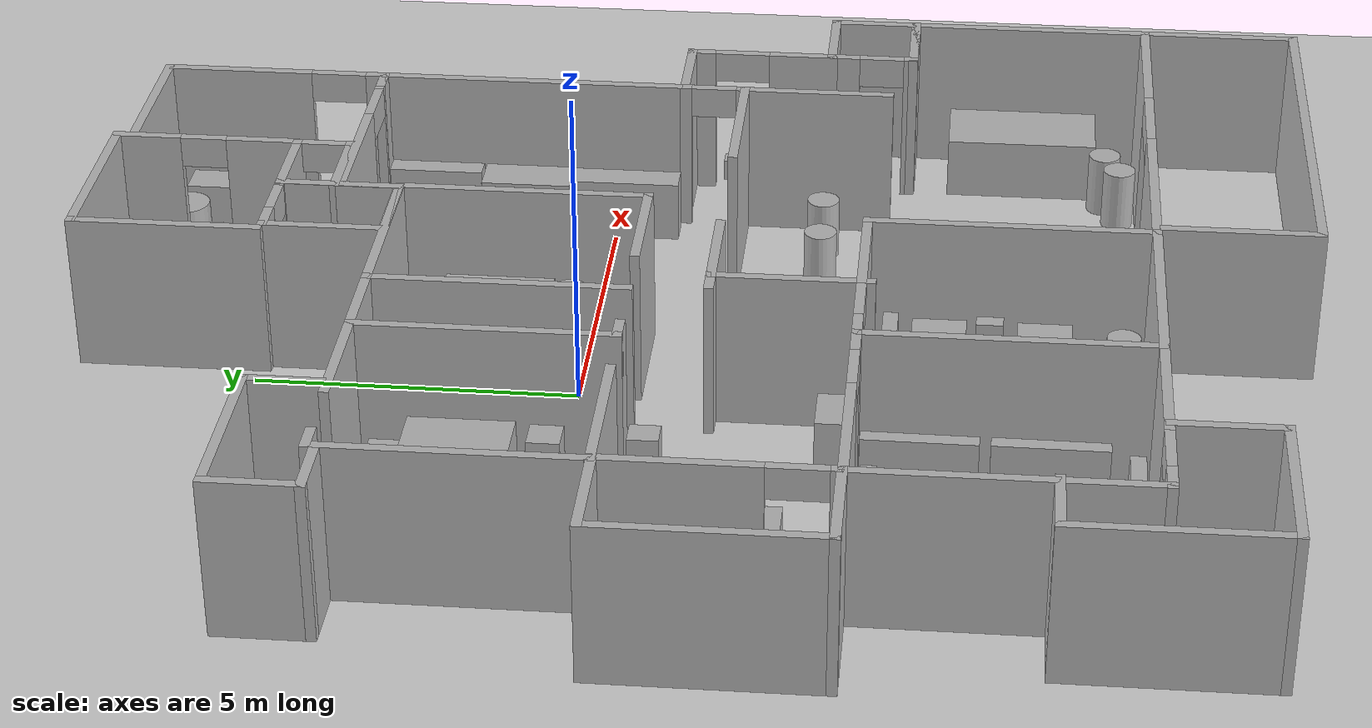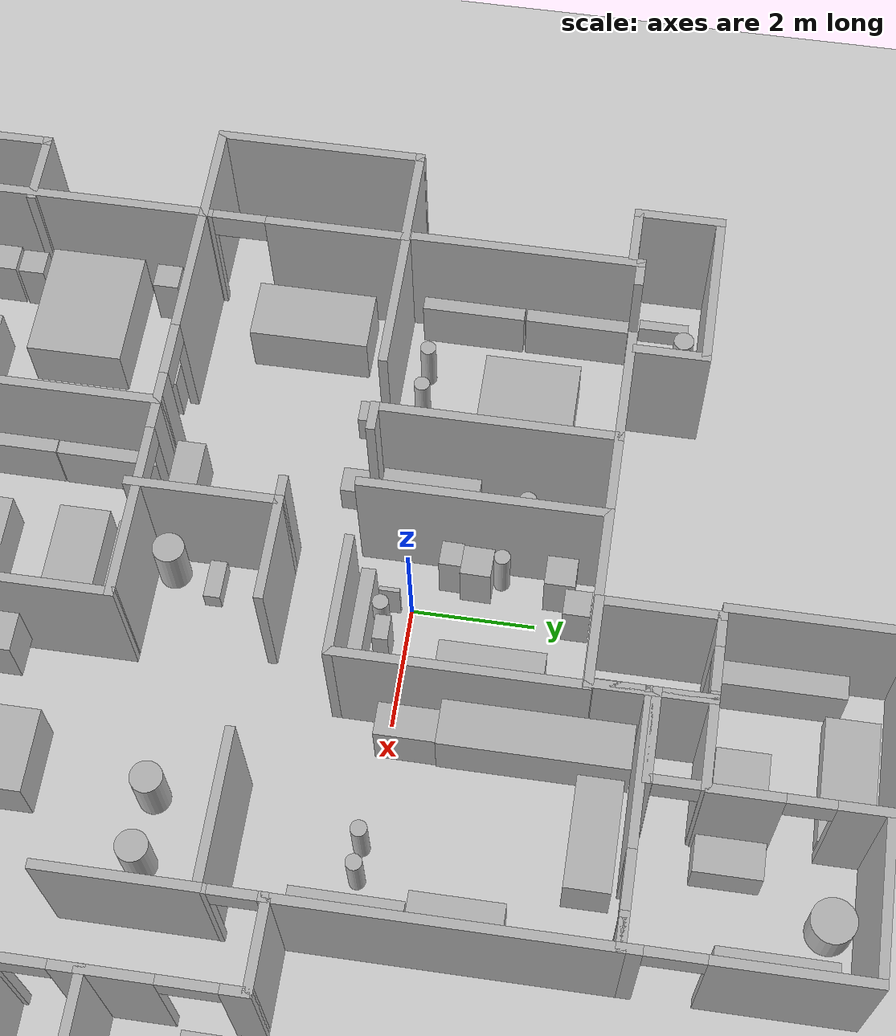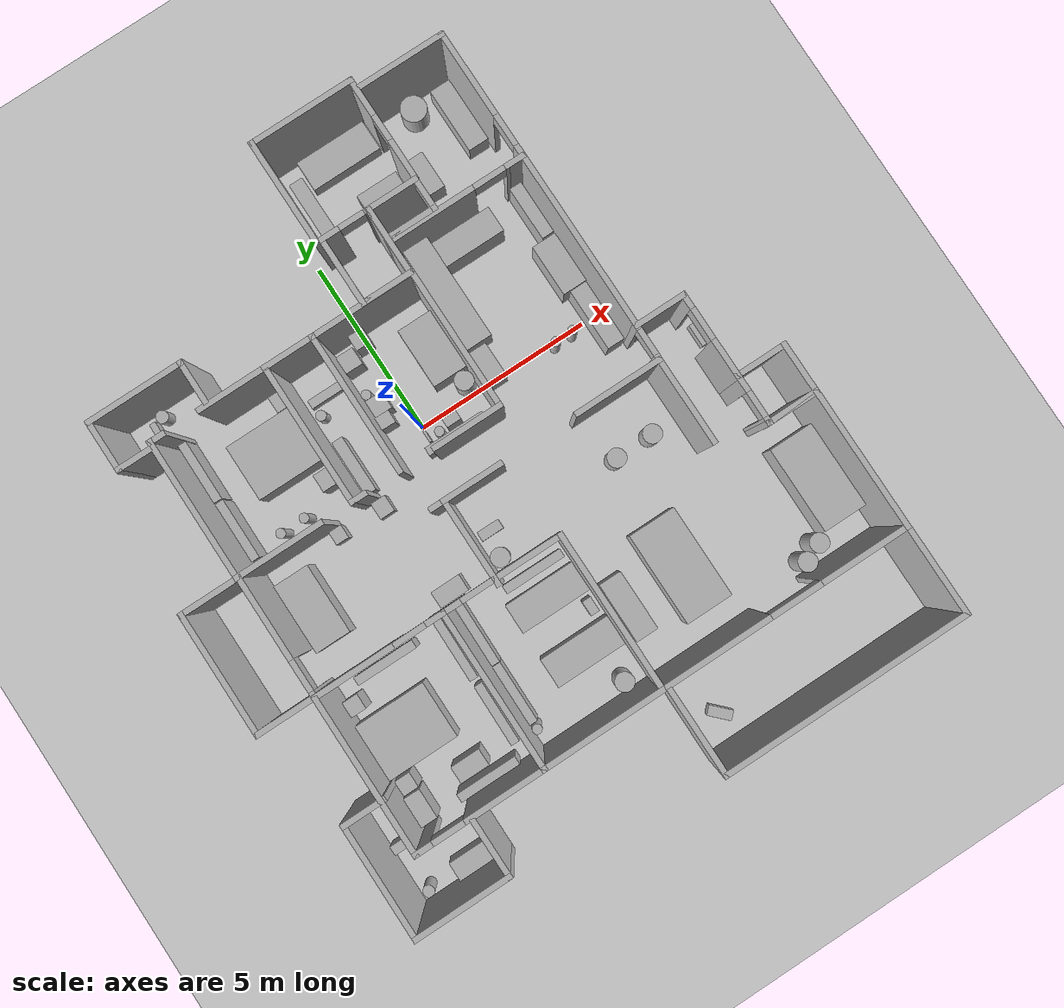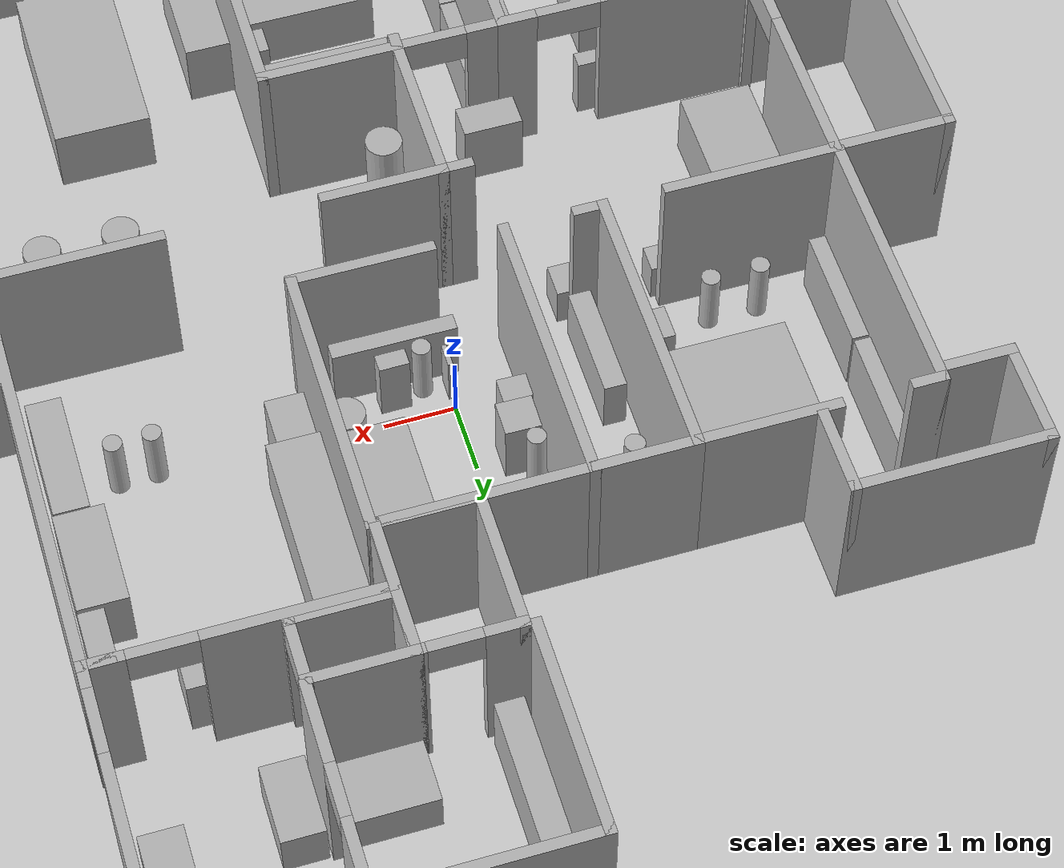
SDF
<?xml version="1.0" ?>
<sdf version="1.8">
  <world name="default">

    <plugin name="gz::sim::systems::Physics" filename="gz-sim-physics-system"/>
    <plugin name="gz::sim::systems::UserCommands" filename="gz-sim-user-commands-system"/>
    <plugin name="gz::sim::systems::SceneBroadcaster" filename="gz-sim-scene-broadcaster-system"/>
    <plugin name="gz::sim::systems::Sensors" filename="gz-sim-sensors-system">
      <render_engine>ogre2</render_engine>
    </plugin>

    <gravity>0 0 -9.8</gravity>
    <magnetic_field>6e-06 2.3e-05 -4.2e-05</magnetic_field>
    <atmosphere type="adiabatic"/>

    <physics type="ode">
      <max_step_size>0.001</max_step_size>
      <real_time_factor>1</real_time_factor>
    </physics>

    <scene>
      <ambient>0.4 0.4 0.4 1</ambient>
      <background>0.7 0.7 0.7 1</background>
      <shadows>true</shadows>
    </scene>

    <light name="sun" type="directional">
      <cast_shadows>true</cast_shadows>
      <pose>0 0 10 0 0 0</pose>
      <diffuse>0.8 0.8 0.8 1</diffuse>
      <specular>0.1 0.1 0.1 1</specular>
      <attenuation>
        <range>1000</range>
        <constant>0.9</constant>
        <linear>0.01</linear>
        <quadratic>0.001</quadratic>
      </attenuation>
      <direction>-0.5 0.5 -1</direction>
    </light>

    <model name="ground_plane">
      <static>true</static>
      <link name="link">
        <collision name="collision">
          <geometry>
            <plane>
              <normal>0 0 1</normal>
              <size>100 100</size>
            </plane>
          </geometry>
          <surface>
            <friction>
              <ode>
                <mu>100</mu>
                <mu2>50</mu2>
              </ode>
            </friction>
          </surface>
        </collision>
        <visual name="visual">
          <geometry>
            <plane>
              <normal>0 0 1</normal>
              <size>100 100</size>
            </plane>
          </geometry>
          <material>
            <ambient>0.8 0.8 0.8 1</ambient>
            <diffuse>0.8 0.8 0.8 1</diffuse>
            <specular>0.8 0.8 0.8 1</specular>
          </material>
        </visual>
      </link>
    </model>

    <model name="cma_escritorio">
      <pose>-1.8304 1.03024 0 0 0 0</pose>
      <link name="Wall_11">
        <collision name="Wall_11_Collision">
          <geometry>
            <box>
              <size>2 0.15 2.5</size>
            </box>
          </geometry>
          <pose>0 0 1.25 0 -0 0</pose>
          <surface>
            <bounce/>
          </surface>
        </collision>
        <visual name="Wall_11_Visual">
          <pose>0 0 1.25 0 -0 0</pose>
          <geometry>
            <box>
              <size>2 0.15 2.5</size>
            </box>
          </geometry>
          <material>
            <ambient>0.7 0.7 0.7 1</ambient>
            <diffuse>0.7 0.7 0.7 1</diffuse>
          </material>
        </visual>
        <pose>-1.4 1.93 0 0 -0 3.14159</pose>
      </link>
      <link name="Wall_2">
        <collision name="Wall_2_Collision">
          <geometry>
            <box>
              <size>4 0.15 2.5</size>
            </box>
          </geometry>
          <pose>0 0 1.25 0 -0 0</pose>
          <surface>
            <bounce/>
          </surface>
        </collision>
        <visual name="Wall_2_Visual">
          <pose>0 0 1.25 0 -0 0</pose>
          <geometry>
            <box>
              <size>4 0.15 2.5</size>
            </box>
          </geometry>
          <material>
            <ambient>0.7 0.7 0.7 1</ambient>
            <diffuse>0.7 0.7 0.7 1</diffuse>
          </material>
        </visual>
        <pose>0.875 0.005 0 0 -0 1.5708</pose>
      </link>
      <link name="Wall_25">
        <collision name="Wall_25_Collision">
          <geometry>
            <box>
              <size>2.5 0.15 2.5</size>
            </box>
          </geometry>
          <pose>0 0 1.25 0 -0 0</pose>
          <surface>
            <bounce/>
          </surface>
        </collision>
        <visual name="Wall_25_Visual">
          <pose>0 0 1.25 0 -0 0</pose>
          <geometry>
            <box>
              <size>2.5 0.15 2.5</size>
            </box>
          </geometry>
          <material>
            <ambient>0.7 0.7 0.7 1</ambient>
            <diffuse>0.7 0.7 0.7 1</diffuse>
          </material>
        </visual>
        <pose>-2.55 -1.93 0 0 -0 3.14159</pose>
      </link>
      <link name="Wall_26">
        <collision name="Wall_26_Collision">
          <geometry>
            <box>
              <size>4 0.15 2.5</size>
            </box>
          </geometry>
          <pose>0 0 1.25 0 -0 0</pose>
          <surface>
            <bounce/>
          </surface>
        </collision>
        <visual name="Wall_26_Visual">
          <pose>0 0 1.25 0 -0 0</pose>
          <geometry>
            <box>
              <size>4 0.15 2.5</size>
            </box>
          </geometry>
          <material>
            <ambient>0.7 0.7 0.7 1</ambient>
            <diffuse>0.7 0.7 0.7 1</diffuse>
          </material>
        </visual>
        <pose>-3.725 -0.005 0 0 -0 1.5708</pose>
      </link>
      <link name="Wall_27">
        <collision name="Wall_27_Collision">
          <geometry>
            <box>
              <size>0.5 0.15 2.5</size>
            </box>
          </geometry>
          <pose>0 0 1.25 0 -0 0</pose>
          <surface>
            <bounce/>
          </surface>
        </collision>
        <visual name="Wall_27_Visual">
          <pose>0 0 1.25 0 -0 0</pose>
          <geometry>
            <box>
              <size>0.5 0.15 2.5</size>
            </box>
          </geometry>
          <material>
            <ambient>0.7 0.7 0.7 1</ambient>
            <diffuse>0.7 0.7 0.7 1</diffuse>
          </material>
        </visual>
        <pose>-3.55 1.92 0 0 -0 0</pose>
      </link>
      <link name="Wall_3">
        <collision name="Wall_3_Collision">
          <geometry>
            <box>
              <size>3 0.15 2.5</size>
            </box>
          </geometry>
          <pose>0 0 1.25 0 -0 0</pose>
          <surface>
            <bounce/>
          </surface>
        </collision>
        <visual name="Wall_3_Visual">
          <pose>0 0 1.25 0 -0 0</pose>
          <geometry>
            <box>
              <size>3 0.15 2.5</size>
            </box>
          </geometry>
          <material>
            <ambient>0.7 0.7 0.7 1</ambient>
            <diffuse>0.7 0.7 0.7 1</diffuse>
          </material>
        </visual>
        <pose>2.3 1.93 0 0 -0 0</pose>
      </link>
      <link name="Wall_4">
        <collision name="Wall_4_Collision">
          <geometry>
            <box>
              <size>4 0.15 2.5</size>
            </box>
          </geometry>
          <pose>0 0 1.25 0 -0 0</pose>
          <surface>
            <bounce/>
          </surface>
        </collision>
        <visual name="Wall_4_Visual">
          <pose>0 0 1.25 0 -0 0</pose>
          <geometry>
            <box>
              <size>4 0.15 2.5</size>
            </box>
          </geometry>
          <material>
            <ambient>0.7 0.7 0.7 1</ambient>
            <diffuse>0.7 0.7 0.7 1</diffuse>
          </material>
        </visual>
        <pose>3.725 0.005 0 0 0 -1.5708</pose>
      </link>
      <link name="Wall_5">
        <collision name="Wall_5_Collision">
          <geometry>
            <box>
              <size>2 0.15 2.5</size>
            </box>
          </geometry>
          <pose>0 0 1.25 0 -0 0</pose>
          <surface>
            <bounce/>
          </surface>
        </collision>
        <visual name="Wall_5_Visual">
          <pose>0 0 1.25 0 -0 0</pose>
          <geometry>
            <box>
              <size>2 0.15 2.5</size>
            </box>
          </geometry>
          <material>
            <ambient>0.7 0.7 0.7 1</ambient>
            <diffuse>0.7 0.7 0.7 1</diffuse>
          </material>
        </visual>
        <pose>2.8 -1.92 0 0 -0 3.14159</pose>
      </link>
      <link name="Wall_7">
        <collision name="Wall_7_Collision">
          <geometry>
            <box>
              <size>1.5 0.15 2.5</size>
            </box>
          </geometry>
          <pose>0 0 1.25 0 -0 0</pose>
          <surface>
            <bounce/>
          </surface>
        </collision>
        <visual name="Wall_7_Visual">
          <pose>0 0 1.25 0 -0 0</pose>
          <geometry>
            <box>
              <size>1.5 0.15 2.5</size>
            </box>
          </geometry>
          <material>
            <ambient>0.7 0.7 0.7 1</ambient>
            <diffuse>0.7 0.7 0.7 1</diffuse>
          </material>
        </visual>
        <pose>0.2 1.93 0 0 -0 3.14159</pose>
      </link>
      <link name="Wall_8">
        <collision name="Wall_8_Collision">
          <geometry>
            <box>
              <size>4 0.15 2.5</size>
            </box>
          </geometry>
          <pose>0 0 1.25 0 -0 0</pose>
          <surface>
            <bounce/>
          </surface>
        </collision>
        <visual name="Wall_8_Visual">
          <pose>0 0 1.25 0 -0 0</pose>
          <geometry>
            <box>
              <size>4 0.15 2.5</size>
            </box>
          </geometry>
          <material>
            <ambient>0.7 0.7 0.7 1</ambient>
            <diffuse>0.7 0.7 0.7 1</diffuse>
          </material>
        </visual>
        <pose>-0.475 0.005 0 0 0 -1.5708</pose>
      </link>
      <link name="Wall_9">
        <collision name="Wall_9_Collision">
          <geometry>
            <box>
              <size>0.5 0.15 2.5</size>
            </box>
          </geometry>
          <pose>0 0 1.25 0 -0 0</pose>
          <surface>
            <bounce/>
          </surface>
        </collision>
        <visual name="Wall_9_Visual">
          <pose>0 0 1.25 0 -0 0</pose>
          <geometry>
            <box>
              <size>0.5 0.15 2.5</size>
            </box>
          </geometry>
          <material>
            <ambient>0.7 0.7 0.7 1</ambient>
            <diffuse>0.7 0.7 0.7 1</diffuse>
          </material>
        </visual>
        <pose>-0.3 -1.92 0 0 -0 0</pose>
      </link>
      <static>true</static>
    </model>

    <model name="cma_banheiro">
      <pose>-5.22928 3.4871 0 0 0 0</pose>
      <link name="Wall_0">
        <collision name="Wall_0_Collision">
          <geometry>
            <box>
              <size>1 0.15 2.5</size>
            </box>
          </geometry>
          <pose>0 0 1.25 0 -0 0</pose>
          <surface>
            <bounce/>
          </surface>
        </collision>
        <visual name="Wall_0_Visual">
          <pose>0 0 1.25 0 -0 0</pose>
          <geometry>
            <box>
              <size>1 0.15 2.5</size>
            </box>
          </geometry>
          <material>
            <ambient>0.7 0.7 0.7 1</ambient>
            <diffuse>0.7 0.7 0.7 1</diffuse>
          </material>
        </visual>
        <pose>-0.875 -0.675 0 0 -0 3.14159</pose>
      </link>
      <link name="Wall_1">
        <collision name="Wall_1_Collision">
          <geometry>
            <box>
              <size>1.5 0.15 2.5</size>
            </box>
          </geometry>
          <pose>0 0 1.25 0 -0 0</pose>
          <surface>
            <bounce/>
          </surface>
        </collision>
        <visual name="Wall_1_Visual">
          <pose>0 0 1.25 0 -0 0</pose>
          <geometry>
            <box>
              <size>1.5 0.15 2.5</size>
            </box>
          </geometry>
          <material>
            <ambient>0.7 0.7 0.7 1</ambient>
            <diffuse>0.7 0.7 0.7 1</diffuse>
          </material>
        </visual>
        <pose>-1.3 0 0 0 -0 1.5708</pose>
      </link>
      <link name="Wall_2">
        <collision name="Wall_2_Collision">
          <geometry>
            <box>
              <size>2.75 0.15 2.5</size>
            </box>
          </geometry>
          <pose>0 0 1.25 0 -0 0</pose>
          <surface>
            <bounce/>
          </surface>
        </collision>
        <visual name="Wall_2_Visual">
          <pose>0 0 1.25 0 -0 0</pose>
          <geometry>
            <box>
              <size>2.75 0.15 2.5</size>
            </box>
          </geometry>
          <material>
            <ambient>0.7 0.7 0.7 1</ambient>
            <diffuse>0.7 0.7 0.7 1</diffuse>
          </material>
        </visual>
        <pose>0 0.675 0 0 -0 0</pose>
      </link>
      <link name="Wall_4">
        <collision name="Wall_4_Collision">
          <geometry>
            <box>
              <size>1.25 0.15 2.5</size>
            </box>
          </geometry>
          <pose>0 0 1.25 0 -0 0</pose>
          <surface>
            <bounce/>
          </surface>
        </collision>
        <visual name="Wall_4_Visual">
          <pose>0 0 1.25 0 -0 0</pose>
          <geometry>
            <box>
              <size>1.25 0.15 2.5</size>
            </box>
          </geometry>
          <material>
            <ambient>0.7 0.7 0.7 1</ambient>
            <diffuse>0.7 0.7 0.7 1</diffuse>
          </material>
        </visual>
        <pose>1.3 0.125 0 0 0 -1.5708</pose>
      </link>
      <static>true</static>
    </model>

    <model name="cma_varanda1">
      <pose>-6.32518 -2.59313 0 0 0 0</pose>
      <link name="Wall_0">
        <pose>0.8 0 0 0 0 -1.5708</pose>
        <visual name="Wall_0_Visual_0">
          <pose>-0.5525 0 1.25 0 -0 0</pose>
          <geometry>
            <box>
              <size>2.395 0.15 2.5</size>
            </box>
          </geometry>
          <material>
            <ambient>0.7 0.7 0.7 1</ambient>
            <diffuse>0.7 0.7 0.7 1</diffuse>
          </material>
        </visual>
        <collision name="Wall_0_Collision_0">
          <geometry>
            <box>
              <size>2.395 0.15 2.5</size>
            </box>
          </geometry>
          <pose>-0.5525 0 1.25 0 -0 0</pose>
          <surface>
            <bounce/>
          </surface>
        </collision>
        <visual name="Wall_0_Visual_1">
          <pose>1.6375 0 1.25 0 -0 0</pose>
          <geometry>
            <box>
              <size>0.225 0.15 2.5</size>
            </box>
          </geometry>
          <material>
            <ambient>0.7 0.7 0.7 1</ambient>
            <diffuse>0.7 0.7 0.7 1</diffuse>
          </material>
        </visual>
        <collision name="Wall_0_Collision_1">
          <geometry>
            <box>
              <size>0.225 0.15 2.5</size>
            </box>
          </geometry>
          <pose>1.6375 0 1.25 0 -0 0</pose>
          <surface>
            <bounce/>
          </surface>
        </collision>
        <visual name="Wall_0_Visual_2">
          <pose>1.085 0 2.25 0 -0 0</pose>
          <geometry>
            <box>
              <size>0.88 0.15 0.5</size>
            </box>
          </geometry>
          <material>
            <ambient>0.7 0.7 0.7 1</ambient>
            <diffuse>0.7 0.7 0.7 1</diffuse>
          </material>
        </visual>
        <collision name="Wall_0_Collision_2">
          <geometry>
            <box>
              <size>0.88 0.15 0.5</size>
            </box>
          </geometry>
          <pose>1.085 0 2.25 0 -0 0</pose>
          <surface>
            <bounce/>
          </surface>
        </collision>
      </link>
      <link name="Wall_1">
        <collision name="Wall_1_Collision">
          <geometry>
            <box>
              <size>1.75 0.15 2.5</size>
            </box>
          </geometry>
          <pose>0 0 1.25 0 -0 0</pose>
          <surface>
            <bounce/>
          </surface>
        </collision>
        <visual name="Wall_1_Visual">
          <pose>0 0 1.25 0 -0 0</pose>
          <geometry>
            <box>
              <size>1.75 0.15 2.5</size>
            </box>
          </geometry>
          <material>
            <ambient>0.7 0.7 0.7 1</ambient>
            <diffuse>0.7 0.7 0.7 1</diffuse>
          </material>
        </visual>
        <pose>0 -1.675 0 0 -0 3.14159</pose>
      </link>
      <link name="Wall_2">
        <collision name="Wall_2_Collision">
          <geometry>
            <box>
              <size>3.5 0.15 2.5</size>
            </box>
          </geometry>
          <pose>0 0 1.25 0 -0 0</pose>
          <surface>
            <bounce/>
          </surface>
        </collision>
        <visual name="Wall_2_Visual">
          <pose>0 0 1.25 0 -0 0</pose>
          <geometry>
            <box>
              <size>3.5 0.15 2.5</size>
            </box>
          </geometry>
          <material>
            <ambient>0.7 0.7 0.7 1</ambient>
            <diffuse>0.7 0.7 0.7 1</diffuse>
          </material>
        </visual>
        <pose>-0.8 0 0 0 -0 1.5708</pose>
      </link>
      <link name="Wall_3">
        <collision name="Wall_3_Collision">
          <geometry>
            <box>
              <size>1.75 0.15 2.5</size>
            </box>
          </geometry>
          <pose>0 0 1.25 0 -0 0</pose>
          <surface>
            <bounce/>
          </surface>
        </collision>
        <visual name="Wall_3_Visual">
          <pose>0 0 1.25 0 -0 0</pose>
          <geometry>
            <box>
              <size>1.75 0.15 2.5</size>
            </box>
          </geometry>
          <material>
            <ambient>0.7 0.7 0.7 1</ambient>
            <diffuse>0.7 0.7 0.7 1</diffuse>
          </material>
        </visual>
        <pose>0 1.675 0 0 -0 0</pose>
      </link>
      <static>true</static>
    </model>

    <model name="cma_quartos">
      <pose>-2.58169 -7.26456 0 0 0 0</pose>
      <link name="Wall_0">
        <collision name="Wall_0_Collision">
          <geometry>
            <box>
              <size>4.5 0.15 2.5</size>
            </box>
          </geometry>
          <pose>0 0 1.25 0 -0 0</pose>
          <surface>
            <bounce/>
          </surface>
        </collision>
        <visual name="Wall_0_Visual">
          <pose>0 0 1.25 0 -0 0</pose>
          <geometry>
            <box>
              <size>4.5 0.15 2.5</size>
            </box>
          </geometry>
          <material>
            <ambient>0.7 0.7 0.7 1</ambient>
            <diffuse>0.7 0.7 0.7 1</diffuse>
          </material>
        </visual>
        <pose>0.645 0.81 0 0 0 -1.5708</pose>
      </link>
      <link name="Wall_1">
        <pose>-1.155 -1.365 0 0 -0 3.14159</pose>
        <visual name="Wall_1_Visual_0">
          <pose>-0.7225 0 1.25 0 -0 0</pose>
          <geometry>
            <box>
              <size>2.305 0.15 2.5</size>
            </box>
          </geometry>
          <material>
            <ambient>0.7 0.7 0.7 1</ambient>
            <diffuse>0.7 0.7 0.7 1</diffuse>
          </material>
        </visual>
        <collision name="Wall_1_Collision_0">
          <geometry>
            <box>
              <size>2.305 0.15 2.5</size>
            </box>
          </geometry>
          <pose>-0.7225 0 1.25 0 -0 0</pose>
          <surface>
            <bounce/>
          </surface>
        </collision>
        <visual name="Wall_1_Visual_1">
          <pose>1.6025 0 1.25 0 -0 0</pose>
          <geometry>
            <box>
              <size>0.545 0.15 2.5</size>
            </box>
          </geometry>
          <material>
            <ambient>0.7 0.7 0.7 1</ambient>
            <diffuse>0.7 0.7 0.7 1</diffuse>
          </material>
        </visual>
        <collision name="Wall_1_Collision_1">
          <geometry>
            <box>
              <size>0.545 0.15 2.5</size>
            </box>
          </geometry>
          <pose>1.6025 0 1.25 0 -0 0</pose>
          <surface>
            <bounce/>
          </surface>
        </collision>
        <visual name="Wall_1_Visual_2">
          <pose>0.88 0 2.25 0 -0 0</pose>
          <geometry>
            <box>
              <size>0.9 0.15 0.5</size>
            </box>
          </geometry>
          <material>
            <ambient>0.7 0.7 0.7 1</ambient>
            <diffuse>0.7 0.7 0.7 1</diffuse>
          </material>
        </visual>
        <collision name="Wall_1_Collision_2">
          <geometry>
            <box>
              <size>0.9 0.15 0.5</size>
            </box>
          </geometry>
          <pose>0.88 0 2.25 0 -0 0</pose>
          <surface>
            <bounce/>
          </surface>
        </collision>
      </link>
      <link name="Wall_10">
        <collision name="Wall_10_Collision">
          <geometry>
            <box>
              <size>1.75 0.15 2.5</size>
            </box>
          </geometry>
          <pose>0 0 1.25 0 -0 0</pose>
          <surface>
            <bounce/>
          </surface>
        </collision>
        <visual name="Wall_10_Visual">
          <pose>0 0 1.25 0 -0 0</pose>
          <geometry>
            <box>
              <size>1.75 0.15 2.5</size>
            </box>
          </geometry>
          <material>
            <ambient>0.7 0.7 0.7 1</ambient>
            <diffuse>0.7 0.7 0.7 1</diffuse>
          </material>
        </visual>
        <pose>-1.395 -2.185 0 0 0 -1.5708</pose>
      </link>
      <link name="Wall_11">
        <collision name="Wall_11_Collision">
          <geometry>
            <box>
              <size>2.75 0.15 2.5</size>
            </box>
          </geometry>
          <pose>0 0 1.25 0 -0 0</pose>
          <surface>
            <bounce/>
          </surface>
        </collision>
        <visual name="Wall_11_Visual">
          <pose>0 0 1.25 0 -0 0</pose>
          <geometry>
            <box>
              <size>2.75 0.15 2.5</size>
            </box>
          </geometry>
          <material>
            <ambient>0.7 0.7 0.7 1</ambient>
            <diffuse>0.7 0.7 0.7 1</diffuse>
          </material>
        </visual>
        <pose>-2.695 -2.985 0 0 -0 3.14159</pose>
      </link>
      <link name="Wall_12">
        <collision name="Wall_12_Collision">
          <geometry>
            <box>
              <size>3.25 0.15 2.5</size>
            </box>
          </geometry>
          <pose>0 0 1.25 0 -0 0</pose>
          <surface>
            <bounce/>
          </surface>
        </collision>
        <visual name="Wall_12_Visual">
          <pose>0 0 1.25 0 -0 0</pose>
          <geometry>
            <box>
              <size>3.25 0.15 2.5</size>
            </box>
          </geometry>
          <material>
            <ambient>0.7 0.7 0.7 1</ambient>
            <diffuse>0.7 0.7 0.7 1</diffuse>
          </material>
        </visual>
        <pose>-3.995 -1.435 0 0 -0 1.5708</pose>
      </link>
      <link name="Wall_13">
        <collision name="Wall_13_Collision">
          <geometry>
            <box>
              <size>1.25 0.15 2.5</size>
            </box>
          </geometry>
          <pose>0 0 1.25 0 -0 0</pose>
          <surface>
            <bounce/>
          </surface>
        </collision>
        <visual name="Wall_13_Visual">
          <pose>0 0 1.25 0 -0 0</pose>
          <geometry>
            <box>
              <size>1.25 0.15 2.5</size>
            </box>
          </geometry>
          <material>
            <ambient>0.7 0.7 0.7 1</ambient>
            <diffuse>0.7 0.7 0.7 1</diffuse>
          </material>
        </visual>
        <pose>-3.445 0.115 0 0 -0 0</pose>
      </link>
      <link name="Wall_2">
        <collision name="Wall_2_Collision">
          <geometry>
            <box>
              <size>4.5 0.15 2.5</size>
            </box>
          </geometry>
          <pose>0 0 1.25 0 -0 0</pose>
          <surface>
            <bounce/>
          </surface>
        </collision>
        <visual name="Wall_2_Visual">
          <pose>0 0 1.25 0 -0 0</pose>
          <geometry>
            <box>
              <size>4.5 0.15 2.5</size>
            </box>
          </geometry>
          <material>
            <ambient>0.7 0.7 0.7 1</ambient>
            <diffuse>0.7 0.7 0.7 1</diffuse>
          </material>
        </visual>
        <pose>-2.955 0.81 0 0 -0 1.5708</pose>
      </link>
      <link name="Wall_3">
        <pose>-1.155 2.985 0 0 -0 0</pose>
        <visual name="Wall_3_Visual_0">
          <pose>-0.7325 0 1.25 0 -0 0</pose>
          <geometry>
            <box>
              <size>2.285 0.15 2.5</size>
            </box>
          </geometry>
          <material>
            <ambient>0.7 0.7 0.7 1</ambient>
            <diffuse>0.7 0.7 0.7 1</diffuse>
          </material>
        </visual>
        <collision name="Wall_3_Collision_0">
          <geometry>
            <box>
              <size>2.285 0.15 2.5</size>
            </box>
          </geometry>
          <pose>-0.7325 0 1.25 0 -0 0</pose>
          <surface>
            <bounce/>
          </surface>
        </collision>
        <visual name="Wall_3_Visual_1">
          <pose>1.5925 0 1.25 0 -0 0</pose>
          <geometry>
            <box>
              <size>0.565 0.15 2.5</size>
            </box>
          </geometry>
          <material>
            <ambient>0.7 0.7 0.7 1</ambient>
            <diffuse>0.7 0.7 0.7 1</diffuse>
          </material>
        </visual>
        <collision name="Wall_3_Collision_1">
          <geometry>
            <box>
              <size>0.565 0.15 2.5</size>
            </box>
          </geometry>
          <pose>1.5925 0 1.25 0 -0 0</pose>
          <surface>
            <bounce/>
          </surface>
        </collision>
        <visual name="Wall_3_Visual_2">
          <pose>0.86 0 2.25 0 -0 0</pose>
          <geometry>
            <box>
              <size>0.9 0.15 0.5</size>
            </box>
          </geometry>
          <material>
            <ambient>0.7 0.7 0.7 1</ambient>
            <diffuse>0.7 0.7 0.7 1</diffuse>
          </material>
        </visual>
        <collision name="Wall_3_Collision_2">
          <geometry>
            <box>
              <size>0.9 0.15 0.5</size>
            </box>
          </geometry>
          <pose>0.86 0 2.25 0 -0 0</pose>
          <surface>
            <bounce/>
          </surface>
        </collision>
      </link>
      <link name="Wall_6">
        <pose>2.32 2.985 0 0 -0 0</pose>
        <visual name="Wall_6_Visual_0">
          <pose>-1.4575 0 1.25 0 -0 0</pose>
          <geometry>
            <box>
              <size>0.585 0.15 2.5</size>
            </box>
          </geometry>
          <material>
            <ambient>0.7 0.7 0.7 1</ambient>
            <diffuse>0.7 0.7 0.7 1</diffuse>
          </material>
        </visual>
        <collision name="Wall_6_Collision_0">
          <geometry>
            <box>
              <size>0.585 0.15 2.5</size>
            </box>
          </geometry>
          <pose>-1.4575 0 1.25 0 -0 0</pose>
          <surface>
            <bounce/>
          </surface>
        </collision>
        <visual name="Wall_6_Visual_1">
          <pose>0.7425 0 1.25 0 -0 0</pose>
          <geometry>
            <box>
              <size>2.015 0.15 2.5</size>
            </box>
          </geometry>
          <material>
            <ambient>0.7 0.7 0.7 1</ambient>
            <diffuse>0.7 0.7 0.7 1</diffuse>
          </material>
        </visual>
        <collision name="Wall_6_Collision_1">
          <geometry>
            <box>
              <size>2.015 0.15 2.5</size>
            </box>
          </geometry>
          <pose>0.7425 0 1.25 0 -0 0</pose>
          <surface>
            <bounce/>
          </surface>
        </collision>
        <visual name="Wall_6_Visual_2">
          <pose>-0.715 0 2.25 0 -0 0</pose>
          <geometry>
            <box>
              <size>0.9 0.15 0.5</size>
            </box>
          </geometry>
          <material>
            <ambient>0.7 0.7 0.7 1</ambient>
            <diffuse>0.7 0.7 0.7 1</diffuse>
          </material>
        </visual>
        <collision name="Wall_6_Collision_2">
          <geometry>
            <box>
              <size>0.9 0.15 0.5</size>
            </box>
          </geometry>
          <pose>-0.715 0 2.25 0 -0 0</pose>
          <surface>
            <bounce/>
          </surface>
        </collision>
      </link>
      <link name="Wall_7">
        <collision name="Wall_7_Collision">
          <geometry>
            <box>
              <size>4.5 0.15 2.5</size>
            </box>
          </geometry>
          <pose>0 0 1.25 0 -0 0</pose>
          <surface>
            <bounce/>
          </surface>
        </collision>
        <visual name="Wall_7_Visual">
          <pose>0 0 1.25 0 -0 0</pose>
          <geometry>
            <box>
              <size>4.5 0.15 2.5</size>
            </box>
          </geometry>
          <material>
            <ambient>0.7 0.7 0.7 1</ambient>
            <diffuse>0.7 0.7 0.7 1</diffuse>
          </material>
        </visual>
        <pose>3.995 0.81 0 0 0 -1.5708</pose>
      </link>
      <link name="Wall_8">
        <collision name="Wall_8_Collision">
          <geometry>
            <box>
              <size>3.5 0.15 2.5</size>
            </box>
          </geometry>
          <pose>0 0 1.25 0 -0 0</pose>
          <surface>
            <bounce/>
          </surface>
        </collision>
        <visual name="Wall_8_Visual">
          <pose>0 0 1.25 0 -0 0</pose>
          <geometry>
            <box>
              <size>3.5 0.15 2.5</size>
            </box>
          </geometry>
          <material>
            <ambient>0.7 0.7 0.7 1</ambient>
            <diffuse>0.7 0.7 0.7 1</diffuse>
          </material>
        </visual>
        <pose>2.32 -1.365 0 0 -0 3.14159</pose>
      </link>
      <static>true</static>
    </model>

    <model name="cma_parede_t">
      <pose>0.159955 -3.24016 0 0 0 0</pose>
      <link name="Wall_15">
        <collision name="Wall_15_Collision">
          <geometry>
            <box>
              <size>2.5 0.15 2.5</size>
            </box>
          </geometry>
          <pose>0 0 1.25 0 -0 0</pose>
          <surface>
            <bounce/>
          </surface>
        </collision>
        <visual name="Wall_15_Visual">
          <pose>0 0 1.25 0 -0 0</pose>
          <geometry>
            <box>
              <size>2.5 0.15 2.5</size>
            </box>
          </geometry>
          <material>
            <ambient>0.7 0.7 0.7 1</ambient>
            <diffuse>0.7 0.7 0.7 1</diffuse>
          </material>
        </visual>
        <pose>-0.625 0 0 0 -0 1.5708</pose>
      </link>
      <link name="Wall_16">
        <collision name="Wall_16_Collision">
          <geometry>
            <box>
              <size>0.5 0.15 2.5</size>
            </box>
          </geometry>
          <pose>0 0 1.25 0 -0 0</pose>
          <surface>
            <bounce/>
          </surface>
        </collision>
        <visual name="Wall_16_Visual">
          <pose>0 0 1.25 0 -0 0</pose>
          <geometry>
            <box>
              <size>0.5 0.15 2.5</size>
            </box>
          </geometry>
          <material>
            <ambient>0.7 0.7 0.7 1</ambient>
            <diffuse>0.7 0.7 0.7 1</diffuse>
          </material>
        </visual>
        <pose>-0.8 1.175 0 0 -0 3.14159</pose>
      </link>
      <link name="Wall_18">
        <collision name="Wall_18_Collision">
          <geometry>
            <box>
              <size>1.75 0.15 2.5</size>
            </box>
          </geometry>
          <pose>0 0 1.25 0 -0 0</pose>
          <surface>
            <bounce/>
          </surface>
        </collision>
        <visual name="Wall_18_Visual">
          <pose>0 0 1.25 0 -0 0</pose>
          <geometry>
            <box>
              <size>1.75 0.15 2.5</size>
            </box>
          </geometry>
          <material>
            <ambient>0.7 0.7 0.7 1</ambient>
            <diffuse>0.7 0.7 0.7 1</diffuse>
          </material>
        </visual>
        <pose>0.175 1.175 0 0 -0 0</pose>
      </link>
      <static>true</static>
    </model>

    <model name="cma_parede_L">
      <pose>4.97628 -6.69992 0 0 0 0</pose>
      <link name="Wall_0">
        <pose>0 -1.925 0 0 -0 0</pose>
        <visual name="Wall_0_Visual_0">
          <pose>-1.985 0 1.25 0 -0 0</pose>
          <geometry>
            <box>
              <size>3.03 0.15 2.5</size>
            </box>
          </geometry>
          <material>
            <ambient>0.7 0.7 0.7 1</ambient>
            <diffuse>0.7 0.7 0.7 1</diffuse>
          </material>
        </visual>
        <collision name="Wall_0_Collision_0">
          <geometry>
            <box>
              <size>3.03 0.15 2.5</size>
            </box>
          </geometry>
          <pose>-1.985 0 1.25 0 -0 0</pose>
          <surface>
            <bounce/>
          </surface>
        </collision>
        <visual name="Wall_0_Visual_1">
          <pose>2.24 0 1.25 0 -0 0</pose>
          <geometry>
            <box>
              <size>2.52 0.15 2.5</size>
            </box>
          </geometry>
          <material>
            <ambient>0.7 0.7 0.7 1</ambient>
            <diffuse>0.7 0.7 0.7 1</diffuse>
          </material>
        </visual>
        <collision name="Wall_0_Collision_1">
          <geometry>
            <box>
              <size>2.52 0.15 2.5</size>
            </box>
          </geometry>
          <pose>2.24 0 1.25 0 -0 0</pose>
          <surface>
            <bounce/>
          </surface>
        </collision>
        <visual name="Wall_0_Visual_2">
          <pose>0.255 0 2.25 0 -0 0</pose>
          <geometry>
            <box>
              <size>1.45 0.15 0.5</size>
            </box>
          </geometry>
          <material>
            <ambient>0.7 0.7 0.7 1</ambient>
            <diffuse>0.7 0.7 0.7 1</diffuse>
          </material>
        </visual>
        <collision name="Wall_0_Collision_2">
          <geometry>
            <box>
              <size>1.45 0.15 0.5</size>
            </box>
          </geometry>
          <pose>0.255 0 2.25 0 -0 0</pose>
          <surface>
            <bounce/>
          </surface>
        </collision>
      </link>
      <link name="Wall_1">
        <collision name="Wall_1_Collision">
          <geometry>
            <box>
              <size>4 0.15 2.5</size>
            </box>
          </geometry>
          <pose>0 0 1.25 0 -0 0</pose>
          <surface>
            <bounce/>
          </surface>
        </collision>
        <visual name="Wall_1_Visual">
          <pose>0 0 1.25 0 -0 0</pose>
          <geometry>
            <box>
              <size>4 0.15 2.5</size>
            </box>
          </geometry>
          <material>
            <ambient>0.7 0.7 0.7 1</ambient>
            <diffuse>0.7 0.7 0.7 1</diffuse>
          </material>
        </visual>
        <pose>3.425 0 0 0 -0 1.5708</pose>
      </link>
      <link name="Wall_2">
        <collision name="Wall_2_Collision">
          <geometry>
            <box>
              <size>1.5 0.15 2.5</size>
            </box>
          </geometry>
          <pose>0 0 1.25 0 -0 0</pose>
          <surface>
            <bounce/>
          </surface>
        </collision>
        <visual name="Wall_2_Visual">
          <pose>0 0 1.25 0 -0 0</pose>
          <geometry>
            <box>
              <size>1.5 0.15 2.5</size>
            </box>
          </geometry>
          <material>
            <ambient>0.7 0.7 0.7 1</ambient>
            <diffuse>0.7 0.7 0.7 1</diffuse>
          </material>
        </visual>
        <pose>2.75 1.925 0 0 -0 3.14159</pose>
      </link>
      <static>true</static>
    </model>

    <model name="cma_lavabo">
      <pose>7.72297 -4.09302 0 0 0 0</pose>
      <link name="Wall_4">
        <pose>-0.675 0 0 0 -0 1.5708</pose>
        <visual name="Wall_4_Visual_0">
          <pose>-0.635 0 1.25 0 -0 0</pose>
          <geometry>
            <box>
              <size>0.23 0.15 2.5</size>
            </box>
          </geometry>
          <material>
            <ambient>0.7 0.7 0.7 1</ambient>
            <diffuse>0.7 0.7 0.7 1</diffuse>
          </material>
        </visual>
        <collision name="Wall_4_Collision_0">
          <geometry>
            <box>
              <size>0.23 0.15 2.5</size>
            </box>
          </geometry>
          <pose>-0.635 0 1.25 0 -0 0</pose>
          <surface>
            <bounce/>
          </surface>
        </collision>
        <visual name="Wall_4_Visual_1">
          <pose>0.48 0 1.25 0 -0 0</pose>
          <geometry>
            <box>
              <size>0.54 0.15 2.5</size>
            </box>
          </geometry>
          <material>
            <ambient>0.7 0.7 0.7 1</ambient>
            <diffuse>0.7 0.7 0.7 1</diffuse>
          </material>
        </visual>
        <collision name="Wall_4_Collision_1">
          <geometry>
            <box>
              <size>0.54 0.15 2.5</size>
            </box>
          </geometry>
          <pose>0.48 0 1.25 0 -0 0</pose>
          <surface>
            <bounce/>
          </surface>
        </collision>
        <visual name="Wall_4_Visual_2">
          <pose>-0.155 0 2.25 0 -0 0</pose>
          <geometry>
            <box>
              <size>0.73 0.15 0.5</size>
            </box>
          </geometry>
          <material>
            <ambient>0.7 0.7 0.7 1</ambient>
            <diffuse>0.7 0.7 0.7 1</diffuse>
          </material>
        </visual>
        <collision name="Wall_4_Collision_2">
          <geometry>
            <box>
              <size>0.73 0.15 0.5</size>
            </box>
          </geometry>
          <pose>-0.155 0 2.25 0 -0 0</pose>
          <surface>
            <bounce/>
          </surface>
        </collision>
      </link>
      <link name="Wall_5">
        <collision name="Wall_5_Collision">
          <geometry>
            <box>
              <size>1.5 0.15 2.5</size>
            </box>
          </geometry>
          <pose>0 0 1.25 0 -0 0</pose>
          <surface>
            <bounce/>
          </surface>
        </collision>
        <visual name="Wall_5_Visual">
          <pose>0 0 1.25 0 -0 0</pose>
          <geometry>
            <box>
              <size>1.5 0.15 2.5</size>
            </box>
          </geometry>
          <material>
            <ambient>0.7 0.7 0.7 1</ambient>
            <diffuse>0.7 0.7 0.7 1</diffuse>
          </material>
        </visual>
        <pose>0 0.675 0 0 -0 0</pose>
      </link>
      <link name="Wall_6">
        <collision name="Wall_6_Collision">
          <geometry>
            <box>
              <size>1.5 0.15 2.5</size>
            </box>
          </geometry>
          <pose>0 0 1.25 0 -0 0</pose>
          <surface>
            <bounce/>
          </surface>
        </collision>
        <visual name="Wall_6_Visual">
          <pose>0 0 1.25 0 -0 0</pose>
          <geometry>
            <box>
              <size>1.5 0.15 2.5</size>
            </box>
          </geometry>
          <material>
            <ambient>0.7 0.7 0.7 1</ambient>
            <diffuse>0.7 0.7 0.7 1</diffuse>
          </material>
        </visual>
        <pose>0.675 0 0 0 0 -1.5708</pose>
      </link>
      <link name="Wall_7">
        <collision name="Wall_7_Collision">
          <geometry>
            <box>
              <size>1.5 0.15 2.5</size>
            </box>
          </geometry>
          <pose>0 0 1.25 0 -0 0</pose>
          <surface>
            <bounce/>
          </surface>
        </collision>
        <visual name="Wall_7_Visual">
          <pose>0 0 1.25 0 -0 0</pose>
          <geometry>
            <box>
              <size>1.5 0.15 2.5</size>
            </box>
          </geometry>
          <material>
            <ambient>0.7 0.7 0.7 1</ambient>
            <diffuse>0.7 0.7 0.7 1</diffuse>
          </material>
        </visual>
        <pose>0 -0.675 0 0 -0 3.14159</pose>
      </link>
      <static>true</static>
    </model>

    <model name="cma_L2">
      <pose>4.51683 -3.24587 0 0 0 0</pose>
      <link name="Wall_10">
        <collision name="Wall_10_Collision">
          <geometry>
            <box>
              <size>2.5 0.15 2.5</size>
            </box>
          </geometry>
          <pose>0 0 1.25 0 -0 0</pose>
          <surface>
            <bounce/>
          </surface>
        </collision>
        <visual name="Wall_10_Visual">
          <pose>0 0 1.25 0 -0 0</pose>
          <geometry>
            <box>
              <size>2.5 0.15 2.5</size>
            </box>
          </geometry>
          <material>
            <ambient>0.7 0.7 0.7 1</ambient>
            <diffuse>0.7 0.7 0.7 1</diffuse>
          </material>
        </visual>
        <pose>1.175 0 0 0 0 -1.5708</pose>
      </link>
      <link name="Wall_9">
        <collision name="Wall_9_Collision">
          <geometry>
            <box>
              <size>2.5 0.15 2.5</size>
            </box>
          </geometry>
          <pose>0 0 1.25 0 -0 0</pose>
          <surface>
            <bounce/>
          </surface>
        </collision>
        <visual name="Wall_9_Visual">
          <pose>0 0 1.25 0 -0 0</pose>
          <geometry>
            <box>
              <size>2.5 0.15 2.5</size>
            </box>
          </geometry>
          <material>
            <ambient>0.7 0.7 0.7 1</ambient>
            <diffuse>0.7 0.7 0.7 1</diffuse>
          </material>
        </visual>
        <pose>0 1.175 0 0 -0 0</pose>
      </link>
      <static>true</static>
    </model>

    <model name="cma_L3">
      <pose>6.37221 -2.26022 0 0 0 0</pose>
      <link name="Wall_12">
        <pose>-0.675 0.75 0 0 -0 1.5708</pose>
        <visual name="Wall_12_Visual_0">
          <pose>-0.46 0 1.25 0 -0 0</pose>
          <geometry>
            <box>
              <size>0.08 0.15 2.5</size>
            </box>
          </geometry>
          <material>
            <ambient>0.7 0.7 0.7 1</ambient>
            <diffuse>0.7 0.7 0.7 1</diffuse>
          </material>
        </visual>
        <collision name="Wall_12_Collision_0">
          <geometry>
            <box>
              <size>0.08 0.15 2.5</size>
            </box>
          </geometry>
          <pose>-0.46 0 1.25 0 -0 0</pose>
          <surface>
            <bounce/>
          </surface>
        </collision>
        <visual name="Wall_12_Visual_1">
          <pose>0.405 0 1.25 0 -0 0</pose>
          <geometry>
            <box>
              <size>0.19 0.15 2.5</size>
            </box>
          </geometry>
          <material>
            <ambient>0.7 0.7 0.7 1</ambient>
            <diffuse>0.7 0.7 0.7 1</diffuse>
          </material>
        </visual>
        <collision name="Wall_12_Collision_1">
          <geometry>
            <box>
              <size>0.19 0.15 2.5</size>
            </box>
          </geometry>
          <pose>0.405 0 1.25 0 -0 0</pose>
          <surface>
            <bounce/>
          </surface>
        </collision>
        <visual name="Wall_12_Visual_2">
          <pose>-0.055 0 2.25 0 -0 0</pose>
          <geometry>
            <box>
              <size>0.73 0.15 0.5</size>
            </box>
          </geometry>
          <material>
            <ambient>0.7 0.7 0.7 1</ambient>
            <diffuse>0.7 0.7 0.7 1</diffuse>
          </material>
        </visual>
        <collision name="Wall_12_Collision_2">
          <geometry>
            <box>
              <size>0.73 0.15 0.5</size>
            </box>
          </geometry>
          <pose>-0.055 0 2.25 0 -0 0</pose>
          <surface>
            <bounce/>
          </surface>
        </collision>
      </link>
      <link name="Wall_13">
        <collision name="Wall_13_Collision">
          <geometry>
            <box>
              <size>1.5 0.15 2.5</size>
            </box>
          </geometry>
          <pose>0 0 1.25 0 -0 0</pose>
          <surface>
            <bounce/>
          </surface>
        </collision>
        <visual name="Wall_13_Visual">
          <pose>0 0 1.25 0 -0 0</pose>
          <geometry>
            <box>
              <size>1.5 0.15 2.5</size>
            </box>
          </geometry>
          <material>
            <ambient>0.7 0.7 0.7 1</ambient>
            <diffuse>0.7 0.7 0.7 1</diffuse>
          </material>
        </visual>
        <pose>0 1.175 0 0 -0 0</pose>
      </link>
      <link name="Wall_14">
        <pose>0.675 0 0 0 0 -1.5708</pose>
        <visual name="Wall_14_Visual_0">
          <pose>-1.0175 0 1.25 0 -0 0</pose>
          <geometry>
            <box>
              <size>0.465 0.15 2.5</size>
            </box>
          </geometry>
          <material>
            <ambient>0.7 0.7 0.7 1</ambient>
            <diffuse>0.7 0.7 0.7 1</diffuse>
          </material>
        </visual>
        <collision name="Wall_14_Collision_0">
          <geometry>
            <box>
              <size>0.465 0.15 2.5</size>
            </box>
          </geometry>
          <pose>-1.0175 0 1.25 0 -0 0</pose>
          <surface>
            <bounce/>
          </surface>
        </collision>
        <visual name="Wall_14_Visual_1">
          <pose>0.6825 0 1.25 0 -0 0</pose>
          <geometry>
            <box>
              <size>1.135 0.15 2.5</size>
            </box>
          </geometry>
          <material>
            <ambient>0.7 0.7 0.7 1</ambient>
            <diffuse>0.7 0.7 0.7 1</diffuse>
          </material>
        </visual>
        <collision name="Wall_14_Collision_1">
          <geometry>
            <box>
              <size>1.135 0.15 2.5</size>
            </box>
          </geometry>
          <pose>0.6825 0 1.25 0 -0 0</pose>
          <surface>
            <bounce/>
          </surface>
        </collision>
        <visual name="Wall_14_Visual_2">
          <pose>-0.335 0 2.25 0 -0 0</pose>
          <geometry>
            <box>
              <size>0.9 0.15 0.5</size>
            </box>
          </geometry>
          <material>
            <ambient>0.7 0.7 0.7 1</ambient>
            <diffuse>0.7 0.7 0.7 1</diffuse>
          </material>
        </visual>
        <collision name="Wall_14_Collision_2">
          <geometry>
            <box>
              <size>0.9 0.15 0.5</size>
            </box>
          </geometry>
          <pose>-0.335 0 2.25 0 -0 0</pose>
          <surface>
            <bounce/>
          </surface>
        </collision>
      </link>
      <static>true</static>
    </model>

    <model name="cma_U">
      <pose>4.97895 -9.92408 0 0 0 0</pose>
      <link name="Wall_16">
        <collision name="Wall_16_Collision">
          <geometry>
            <box>
              <size>2.5 0.15 2.5</size>
            </box>
          </geometry>
          <pose>0 0 1.25 0 -0 0</pose>
          <surface>
            <bounce/>
          </surface>
        </collision>
        <visual name="Wall_16_Visual">
          <pose>0 0 1.25 0 -0 0</pose>
          <geometry>
            <box>
              <size>2.5 0.15 2.5</size>
            </box>
          </geometry>
          <material>
            <ambient>0.7 0.7 0.7 1</ambient>
            <diffuse>0.7 0.7 0.7 1</diffuse>
          </material>
        </visual>
        <pose>-3.425 0 0 0 0 -1.5708</pose>
      </link>
      <link name="Wall_17">
        <collision name="Wall_17_Collision">
          <geometry>
            <box>
              <size>7 0.15 2.5</size>
            </box>
          </geometry>
          <pose>0 0 1.25 0 -0 0</pose>
          <surface>
            <bounce/>
          </surface>
        </collision>
        <visual name="Wall_17_Visual">
          <pose>0 0 1.25 0 -0 0</pose>
          <geometry>
            <box>
              <size>7 0.15 2.5</size>
            </box>
          </geometry>
          <material>
            <ambient>0.7 0.7 0.7 1</ambient>
            <diffuse>0.7 0.7 0.7 1</diffuse>
          </material>
        </visual>
        <pose>0 -1.175 0 0 -0 0</pose>
      </link>
      <link name="Wall_18">
        <collision name="Wall_18_Collision">
          <geometry>
            <box>
              <size>2.5 0.15 2.5</size>
            </box>
          </geometry>
          <pose>0 0 1.25 0 -0 0</pose>
          <surface>
            <bounce/>
          </surface>
        </collision>
        <visual name="Wall_18_Visual">
          <pose>0 0 1.25 0 -0 0</pose>
          <geometry>
            <box>
              <size>2.5 0.15 2.5</size>
            </box>
          </geometry>
          <material>
            <ambient>0.7 0.7 0.7 1</ambient>
            <diffuse>0.7 0.7 0.7 1</diffuse>
          </material>
        </visual>
        <pose>3.425 0 0 0 -0 1.5708</pose>
      </link>
      <static>true</static>
    </model>

    <model name="cma_L5">
      <pose>3.77502 1.45512 0 0 0 0</pose>
      <link name="Wall_0">
        <collision name="Wall_0_Collision">
          <geometry>
            <box>
              <size>1 0.15 2.5</size>
            </box>
          </geometry>
          <pose>0 0 1.25 0 -0 0</pose>
          <surface>
            <bounce/>
          </surface>
        </collision>
        <visual name="Wall_0_Visual">
          <pose>0 0 1.25 0 -0 0</pose>
          <geometry>
            <box>
              <size>1 0.15 2.5</size>
            </box>
          </geometry>
          <material>
            <ambient>0.7 0.7 0.7 1</ambient>
            <diffuse>0.7 0.7 0.7 1</diffuse>
          </material>
        </visual>
        <pose>-1.925 2 0 0 -0 1.5708</pose>
      </link>
      <link name="Wall_1">
        <pose>0 2.425 0 0 -0 0</pose>
        <visual name="Wall_1_Visual_0">
          <pose>-0.7525 0 1.25 0 -0 0</pose>
          <geometry>
            <box>
              <size>2.495 0.15 2.5</size>
            </box>
          </geometry>
          <material>
            <ambient>0.7 0.7 0.7 1</ambient>
            <diffuse>0.7 0.7 0.7 1</diffuse>
          </material>
        </visual>
        <collision name="Wall_1_Collision_0">
          <geometry>
            <box>
              <size>2.495 0.15 2.5</size>
            </box>
          </geometry>
          <pose>-0.7525 0 1.25 0 -0 0</pose>
          <surface>
            <bounce/>
          </surface>
        </collision>
        <visual name="Wall_1_Visual_1">
          <pose>1.6975 0 1.25 0 -0 0</pose>
          <geometry>
            <box>
              <size>0.605 0.15 2.5</size>
            </box>
          </geometry>
          <material>
            <ambient>0.7 0.7 0.7 1</ambient>
            <diffuse>0.7 0.7 0.7 1</diffuse>
          </material>
        </visual>
        <collision name="Wall_1_Collision_1">
          <geometry>
            <box>
              <size>0.605 0.15 2.5</size>
            </box>
          </geometry>
          <pose>1.6975 0 1.25 0 -0 0</pose>
          <surface>
            <bounce/>
          </surface>
        </collision>
        <visual name="Wall_1_Visual_2">
          <pose>0.945 0 2.25 0 -0 0</pose>
          <geometry>
            <box>
              <size>0.9 0.15 0.5</size>
            </box>
          </geometry>
          <material>
            <ambient>0.7 0.7 0.7 1</ambient>
            <diffuse>0.7 0.7 0.7 1</diffuse>
          </material>
        </visual>
        <collision name="Wall_1_Collision_2">
          <geometry>
            <box>
              <size>0.9 0.15 0.5</size>
            </box>
          </geometry>
          <pose>0.945 0 2.25 0 -0 0</pose>
          <surface>
            <bounce/>
          </surface>
        </collision>
      </link>
      <link name="Wall_3">
        <collision name="Wall_3_Collision">
          <geometry>
            <box>
              <size>5 0.15 2.5</size>
            </box>
          </geometry>
          <pose>0 0 1.25 0 -0 0</pose>
          <surface>
            <bounce/>
          </surface>
        </collision>
        <visual name="Wall_3_Visual">
          <pose>0 0 1.25 0 -0 0</pose>
          <geometry>
            <box>
              <size>5 0.15 2.5</size>
            </box>
          </geometry>
          <material>
            <ambient>0.7 0.7 0.7 1</ambient>
            <diffuse>0.7 0.7 0.7 1</diffuse>
          </material>
        </visual>
        <pose>1.925 0 0 0 0 -1.5708</pose>
      </link>
      <static>true</static>
    </model>

    <model name="cma_dispensa">
      <pose>2.52584 4.40119 0 0 0 0</pose>
      <link name="Wall_5">
        <collision name="Wall_5_Collision">
          <geometry>
            <box>
              <size>1 0.15 2.5</size>
            </box>
          </geometry>
          <pose>0 0 1.25 0 -0 0</pose>
          <surface>
            <bounce/>
          </surface>
        </collision>
        <visual name="Wall_5_Visual">
          <pose>0 0 1.25 0 -0 0</pose>
          <geometry>
            <box>
              <size>1 0.15 2.5</size>
            </box>
          </geometry>
          <material>
            <ambient>0.7 0.7 0.7 1</ambient>
            <diffuse>0.7 0.7 0.7 1</diffuse>
          </material>
        </visual>
        <pose>-0.675 0 0 0 -0 1.5708</pose>
      </link>
      <link name="Wall_6">
        <collision name="Wall_6_Collision">
          <geometry>
            <box>
              <size>1.5 0.15 2.5</size>
            </box>
          </geometry>
          <pose>0 0 1.25 0 -0 0</pose>
          <surface>
            <bounce/>
          </surface>
        </collision>
        <visual name="Wall_6_Visual">
          <pose>0 0 1.25 0 -0 0</pose>
          <geometry>
            <box>
              <size>1.5 0.15 2.5</size>
            </box>
          </geometry>
          <material>
            <ambient>0.7 0.7 0.7 1</ambient>
            <diffuse>0.7 0.7 0.7 1</diffuse>
          </material>
        </visual>
        <pose>0 0.425 0 0 -0 0</pose>
      </link>
      <link name="Wall_7">
        <pose>0.675 0 0 0 0 -1.5708</pose>
        <visual name="Wall_7_Visual_0">
          <pose>-0.4275 0 1.25 0 -0 0</pose>
          <geometry>
            <box>
              <size>0.145 0.15 2.5</size>
            </box>
          </geometry>
          <material>
            <ambient>0.7 0.7 0.7 1</ambient>
            <diffuse>0.7 0.7 0.7 1</diffuse>
          </material>
        </visual>
        <collision name="Wall_7_Collision_0">
          <geometry>
            <box>
              <size>0.145 0.15 2.5</size>
            </box>
          </geometry>
          <pose>-0.4275 0 1.25 0 -0 0</pose>
          <surface>
            <bounce/>
          </surface>
        </collision>
        <visual name="Wall_7_Visual_1">
          <pose>0.4225 0 1.25 0 -0 0</pose>
          <geometry>
            <box>
              <size>0.155 0.15 2.5</size>
            </box>
          </geometry>
          <material>
            <ambient>0.7 0.7 0.7 1</ambient>
            <diffuse>0.7 0.7 0.7 1</diffuse>
          </material>
        </visual>
        <collision name="Wall_7_Collision_1">
          <geometry>
            <box>
              <size>0.155 0.15 2.5</size>
            </box>
          </geometry>
          <pose>0.4225 0 1.25 0 -0 0</pose>
          <surface>
            <bounce/>
          </surface>
        </collision>
        <visual name="Wall_7_Visual_2">
          <pose>-0.005 0 2.25 0 -0 0</pose>
          <geometry>
            <box>
              <size>0.7 0.15 0.5</size>
            </box>
          </geometry>
          <material>
            <ambient>0.7 0.7 0.7 1</ambient>
            <diffuse>0.7 0.7 0.7 1</diffuse>
          </material>
        </visual>
        <collision name="Wall_7_Collision_2">
          <geometry>
            <box>
              <size>0.7 0.15 0.5</size>
            </box>
          </geometry>
          <pose>-0.005 0 2.25 0 -0 0</pose>
          <surface>
            <bounce/>
          </surface>
        </collision>
      </link>
      <link name="Wall_8">
        <collision name="Wall_8_Collision">
          <geometry>
            <box>
              <size>1.5 0.15 2.5</size>
            </box>
          </geometry>
          <pose>0 0 1.25 0 -0 0</pose>
          <surface>
            <bounce/>
          </surface>
        </collision>
        <visual name="Wall_8_Visual">
          <pose>0 0 1.25 0 -0 0</pose>
          <geometry>
            <box>
              <size>1.5 0.15 2.5</size>
            </box>
          </geometry>
          <material>
            <ambient>0.7 0.7 0.7 1</ambient>
            <diffuse>0.7 0.7 0.7 1</diffuse>
          </material>
        </visual>
        <pose>0 -0.425 0 0 -0 3.14159</pose>
      </link>
      <static>true</static>
    </model>

    <model name="cma_banheiro_e">
      <pose>1.18358 3.89879 0 0 0 0</pose>
      <link name="Wall_10">
        <collision name="Wall_10_Collision">
          <geometry>
            <box>
              <size>1.5 0.15 2.5</size>
            </box>
          </geometry>
          <pose>0 0 1.25 0 -0 0</pose>
          <surface>
            <bounce/>
          </surface>
        </collision>
        <visual name="Wall_10_Visual">
          <pose>0 0 1.25 0 -0 0</pose>
          <geometry>
            <box>
              <size>1.5 0.15 2.5</size>
            </box>
          </geometry>
          <material>
            <ambient>0.7 0.7 0.7 1</ambient>
            <diffuse>0.7 0.7 0.7 1</diffuse>
          </material>
        </visual>
        <pose>0 -0.925 0 0 -0 3.14159</pose>
      </link>
      <link name="Wall_11">
        <collision name="Wall_11_Collision">
          <geometry>
            <box>
              <size>2 0.15 2.5</size>
            </box>
          </geometry>
          <pose>0 0 1.25 0 -0 0</pose>
          <surface>
            <bounce/>
          </surface>
        </collision>
        <visual name="Wall_11_Visual">
          <pose>0 0 1.25 0 -0 0</pose>
          <geometry>
            <box>
              <size>2 0.15 2.5</size>
            </box>
          </geometry>
          <material>
            <ambient>0.7 0.7 0.7 1</ambient>
            <diffuse>0.7 0.7 0.7 1</diffuse>
          </material>
        </visual>
        <pose>-0.675 0 0 0 -0 1.5708</pose>
      </link>
      <link name="Wall_12">
        <pose>0 0.925 0 0 -0 0</pose>
        <visual name="Wall_12_Visual_0">
          <pose>-0.4625 0 1.25 0 -0 0</pose>
          <geometry>
            <box>
              <size>0.575 0.15 2.5</size>
            </box>
          </geometry>
          <material>
            <ambient>0.7 0.7 0.7 1</ambient>
            <diffuse>0.7 0.7 0.7 1</diffuse>
          </material>
        </visual>
        <collision name="Wall_12_Collision_0">
          <geometry>
            <box>
              <size>0.575 0.15 2.5</size>
            </box>
          </geometry>
          <pose>-0.4625 0 1.25 0 -0 0</pose>
          <surface>
            <bounce/>
          </surface>
        </collision>
        <visual name="Wall_12_Visual_1">
          <pose>0.6475 0 1.25 0 -0 0</pose>
          <geometry>
            <box>
              <size>0.205 0.15 2.5</size>
            </box>
          </geometry>
          <material>
            <ambient>0.7 0.7 0.7 1</ambient>
            <diffuse>0.7 0.7 0.7 1</diffuse>
          </material>
        </visual>
        <collision name="Wall_12_Collision_1">
          <geometry>
            <box>
              <size>0.205 0.15 2.5</size>
            </box>
          </geometry>
          <pose>0.6475 0 1.25 0 -0 0</pose>
          <surface>
            <bounce/>
          </surface>
        </collision>
        <visual name="Wall_12_Visual_2">
          <pose>0.185 0 2.25 0 -0 0</pose>
          <geometry>
            <box>
              <size>0.72 0.15 0.5</size>
            </box>
          </geometry>
          <material>
            <ambient>0.7 0.7 0.7 1</ambient>
            <diffuse>0.7 0.7 0.7 1</diffuse>
          </material>
        </visual>
        <collision name="Wall_12_Collision_2">
          <geometry>
            <box>
              <size>0.72 0.15 0.5</size>
            </box>
          </geometry>
          <pose>0.185 0 2.25 0 -0 0</pose>
          <surface>
            <bounce/>
          </surface>
        </collision>
      </link>
      <link name="Wall_13">
        <collision name="Wall_13_Collision">
          <geometry>
            <box>
              <size>2 0.15 2.5</size>
            </box>
          </geometry>
          <pose>0 0 1.25 0 -0 0</pose>
          <surface>
            <bounce/>
          </surface>
        </collision>
        <visual name="Wall_13_Visual">
          <pose>0 0 1.25 0 -0 0</pose>
          <geometry>
            <box>
              <size>2 0.15 2.5</size>
            </box>
          </geometry>
          <material>
            <ambient>0.7 0.7 0.7 1</ambient>
            <diffuse>0.7 0.7 0.7 1</diffuse>
          </material>
        </visual>
        <pose>0.675 0 0 0 0 -1.5708</pose>
      </link>
      <static>true</static>
    </model>

    <model name="cma_qe">
      <pose>1.79561 6.31228 0 0 0 0</pose>
      <link name="Wall_15">
        <collision name="Wall_15_Collision">
          <geometry>
            <box>
              <size>3 0.15 2.5</size>
            </box>
          </geometry>
          <pose>0 0 1.25 0 -0 0</pose>
          <surface>
            <bounce/>
          </surface>
        </collision>
        <visual name="Wall_15_Visual">
          <pose>0 0 1.25 0 -0 0</pose>
          <geometry>
            <box>
              <size>3 0.15 2.5</size>
            </box>
          </geometry>
          <material>
            <ambient>0.7 0.7 0.7 1</ambient>
            <diffuse>0.7 0.7 0.7 1</diffuse>
          </material>
        </visual>
        <pose>-1.425 0 0 0 -0 1.5708</pose>
      </link>
      <link name="Wall_16">
        <collision name="Wall_16_Collision">
          <geometry>
            <box>
              <size>3 0.15 2.5</size>
            </box>
          </geometry>
          <pose>0 0 1.25 0 -0 0</pose>
          <surface>
            <bounce/>
          </surface>
        </collision>
        <visual name="Wall_16_Visual">
          <pose>0 0 1.25 0 -0 0</pose>
          <geometry>
            <box>
              <size>3 0.15 2.5</size>
            </box>
          </geometry>
          <material>
            <ambient>0.7 0.7 0.7 1</ambient>
            <diffuse>0.7 0.7 0.7 1</diffuse>
          </material>
        </visual>
        <pose>0 1.425 0 0 -0 0</pose>
      </link>
      <link name="Wall_17">
        <pose>1.425 0 0 0 0 -1.5708</pose>
        <visual name="Wall_17_Visual_0">
          <pose>-0.945 0 1.25 0 -0 0</pose>
          <geometry>
            <box>
              <size>1.11 0.15 2.5</size>
            </box>
          </geometry>
          <material>
            <ambient>0.7 0.7 0.7 1</ambient>
            <diffuse>0.7 0.7 0.7 1</diffuse>
          </material>
        </visual>
        <collision name="Wall_17_Collision_0">
          <geometry>
            <box>
              <size>1.11 0.15 2.5</size>
            </box>
          </geometry>
          <pose>-0.945 0 1.25 0 -0 0</pose>
          <surface>
            <bounce/>
          </surface>
        </collision>
        <visual name="Wall_17_Visual_1">
          <pose>0.92 0 1.25 0 -0 0</pose>
          <geometry>
            <box>
              <size>1.16 0.15 2.5</size>
            </box>
          </geometry>
          <material>
            <ambient>0.7 0.7 0.7 1</ambient>
            <diffuse>0.7 0.7 0.7 1</diffuse>
          </material>
        </visual>
        <collision name="Wall_17_Collision_1">
          <geometry>
            <box>
              <size>1.16 0.15 2.5</size>
            </box>
          </geometry>
          <pose>0.92 0 1.25 0 -0 0</pose>
          <surface>
            <bounce/>
          </surface>
        </collision>
        <visual name="Wall_17_Visual_2">
          <pose>-0.025 0 2.25 0 -0 0</pose>
          <geometry>
            <box>
              <size>0.73 0.15 0.5</size>
            </box>
          </geometry>
          <material>
            <ambient>0.7 0.7 0.7 1</ambient>
            <diffuse>0.7 0.7 0.7 1</diffuse>
          </material>
        </visual>
        <collision name="Wall_17_Collision_2">
          <geometry>
            <box>
              <size>0.73 0.15 0.5</size>
            </box>
          </geometry>
          <pose>-0.025 0 2.25 0 -0 0</pose>
          <surface>
            <bounce/>
          </surface>
        </collision>
      </link>
      <static>true</static>
    </model>

    <model name="cma_area2">
      <pose>4.52275 5.67862 0 0 0 0</pose>
      <link name="Wall_23">
        <collision name="Wall_23_Collision">
          <geometry>
            <box>
              <size>2.5 0.15 2.5</size>
            </box>
          </geometry>
          <pose>0 0 1.25 0 -0 0</pose>
          <surface>
            <bounce/>
          </surface>
        </collision>
        <visual name="Wall_23_Visual">
          <pose>0 0 1.25 0 -0 0</pose>
          <geometry>
            <box>
              <size>2.5 0.15 2.5</size>
            </box>
          </geometry>
          <material>
            <ambient>0.7 0.7 0.7 1</ambient>
            <diffuse>0.7 0.7 0.7 1</diffuse>
          </material>
        </visual>
        <pose>0 1.8 0 0 -0 0</pose>
      </link>
      <link name="Wall_24">
        <pose>1.175 0 0 0 0 -1.5708</pose>
        <visual name="Wall_24_Visual_0">
          <pose>-0.6425 0 1.25 0 -0 0</pose>
          <geometry>
            <box>
              <size>2.465 0.15 2.5</size>
            </box>
          </geometry>
          <material>
            <ambient>0.7 0.7 0.7 1</ambient>
            <diffuse>0.7 0.7 0.7 1</diffuse>
          </material>
        </visual>
        <collision name="Wall_24_Collision_0">
          <geometry>
            <box>
              <size>2.465 0.15 2.5</size>
            </box>
          </geometry>
          <pose>-0.6425 0 1.25 0 -0 0</pose>
          <surface>
            <bounce/>
          </surface>
        </collision>
        <visual name="Wall_24_Visual_1">
          <pose>1.6825 0 1.25 0 -0 0</pose>
          <geometry>
            <box>
              <size>0.385 0.15 2.5</size>
            </box>
          </geometry>
          <material>
            <ambient>0.7 0.7 0.7 1</ambient>
            <diffuse>0.7 0.7 0.7 1</diffuse>
          </material>
        </visual>
        <collision name="Wall_24_Collision_1">
          <geometry>
            <box>
              <size>0.385 0.15 2.5</size>
            </box>
          </geometry>
          <pose>1.6825 0 1.25 0 -0 0</pose>
          <surface>
            <bounce/>
          </surface>
        </collision>
        <visual name="Wall_24_Visual_2">
          <pose>1.04 0 2.25 0 -0 0</pose>
          <geometry>
            <box>
              <size>0.9 0.15 0.5</size>
            </box>
          </geometry>
          <material>
            <ambient>0.7 0.7 0.7 1</ambient>
            <diffuse>0.7 0.7 0.7 1</diffuse>
          </material>
        </visual>
        <collision name="Wall_24_Collision_2">
          <geometry>
            <box>
              <size>0.9 0.15 0.5</size>
            </box>
          </geometry>
          <pose>1.04 0 2.25 0 -0 0</pose>
          <surface>
            <bounce/>
          </surface>
        </collision>
      </link>
      <link name="Wall_25">
        <collision name="Wall_25_Collision">
          <geometry>
            <box>
              <size>0.5 0.15 2.5</size>
            </box>
          </geometry>
          <pose>0 0 1.25 0 -0 0</pose>
          <surface>
            <bounce/>
          </surface>
        </collision>
        <visual name="Wall_25_Visual">
          <pose>0 0 1.25 0 -0 0</pose>
          <geometry>
            <box>
              <size>0.5 0.15 2.5</size>
            </box>
          </geometry>
          <material>
            <ambient>0.7 0.7 0.7 1</ambient>
            <diffuse>0.7 0.7 0.7 1</diffuse>
          </material>
        </visual>
        <pose>1 -1.8 0 0 -0 3.14159</pose>
      </link>
      <static>true</static>
    </model>

    <model name="cma_armario">
      <link name="link_0">
        <pose>1.32157 0.885178 0.5 0 -0 0</pose>
        <visual name="visual">
          <pose>0 0 0 0 -0 0</pose>
          <geometry>
            <box>
              <size>1.71877 0.234069 1</size>
            </box>
          </geometry>
          <material>
            <ambient>0.7 0.7 0.7 1</ambient>
            <diffuse>0.7 0.7 0.7 1</diffuse>
          </material>
        </visual>
        <collision name="collision">
          <pose>0 0 0 0 -0 0</pose>
          <geometry>
            <box>
              <size>1.71877 0.234069 1</size>
            </box>
          </geometry>
          <surface>
            <friction>
              <ode>
                <mu>1</mu>
                <mu2>1</mu2>
              </ode>
            </friction>
          </surface>
        </collision>
      </link>
      <static>true</static>
      <pose>-0.670509 -1.58172 1e-06 -1e-06 1e-06 -0.000321</pose>
    </model>

    <model name="cma_picador_0">
      <link name="link_2">
        <pose>-0.7258 -1.69104 0 0 -0 0</pose>
        <visual name="visual">
          <pose>0 0 0 0 -0 0</pose>
          <geometry>
            <box>
              <size>0.416688 0.25134 1</size>
            </box>
          </geometry>
          <material>
            <ambient>0.7 0.7 0.7 1</ambient>
            <diffuse>0.7 0.7 0.7 1</diffuse>
          </material>
        </visual>
        <collision name="collision">
          <pose>0 0 0 0 -0 0</pose>
          <geometry>
            <box>
              <size>0.416688 0.25134 1</size>
            </box>
          </geometry>
          <surface>
            <friction>
              <ode>
                <mu>1</mu>
                <mu2>1</mu2>
              </ode>
            </friction>
          </surface>
        </collision>
      </link>
      <static>true</static>
      <pose>1.46993 1.36075 0.499999 0 2e-06 0.01021</pose>
    </model>

    <model name="cma_lixo">
      <link name="link_1">
        <pose>0.882962 1.81586 0.5 0 -0 0</pose>
        <visual name="visual">
          <pose>0 0 0 0 -0 0</pose>
          <geometry>
            <cylinder>
              <radius>0.131112</radius>
              <length>1</length>
            </cylinder>
          </geometry>
          <material>
            <ambient>0.7 0.7 0.7 1</ambient>
            <diffuse>0.7 0.7 0.7 1</diffuse>
          </material>
        </visual>
        <collision name="collision">
          <pose>0 0 0 0 -0 0</pose>
          <geometry>
            <cylinder>
              <radius>0.131112</radius>
              <length>1</length>
            </cylinder>
          </geometry>
          <surface>
            <friction>
              <ode>
                <mu>1</mu>
                <mu2>1</mu2>
              </ode>
            </friction>
          </surface>
        </collision>
      </link>
      <static>true</static>
      <pose>-1.35785 -1.52544 -5e-06 0 0 -0.543097</pose>
    </model>

    <model name="cma_cesto">
      <link name="link_1">
        <pose>-0.329659 -1.55494 0 0 -0 0</pose>
        <visual name="visual">
          <pose>0 0 0 0 -0 0</pose>
          <geometry>
            <cylinder>
              <radius>0.258792</radius>
              <length>1</length>
            </cylinder>
          </geometry>
          <material>
            <ambient>0.7 0.7 0.7 1</ambient>
            <diffuse>0.7 0.7 0.7 1</diffuse>
          </material>
        </visual>
        <collision name="collision">
          <pose>0 0 0 0 -0 0</pose>
          <geometry>
            <cylinder>
              <radius>0.258792</radius>
              <length>1</length>
            </cylinder>
          </geometry>
          <surface>
            <friction>
              <ode>
                <mu>1</mu>
                <mu2>1</mu2>
              </ode>
            </friction>
          </surface>
        </collision>
      </link>
      <static>true</static>
      <pose>1.91097 1.85863 0.499998 0 0 -0.013205</pose>
    </model>

    <model name="cma_sofa_2_lugares">
      <link name="link_0">
        <pose>-0.034013 -0.039828 0 0 -0 0</pose>
        <visual name="visual">
          <pose>0 0 0 0 -0 0</pose>
          <geometry>
            <box>
              <size>0.977147 1.69968 1</size>
            </box>
          </geometry>
          <material>
            <ambient>0.7 0.7 0.7 1</ambient>
            <diffuse>0.7 0.7 0.7 1</diffuse>
          </material>
        </visual>
        <collision name="collision">
          <pose>0 0 0 0 -0 0</pose>
          <geometry>
            <box>
              <size>0.977147 1.69968 1</size>
            </box>
          </geometry>
          <surface>
            <friction>
              <ode>
                <mu>1</mu>
                <mu2>1</mu2>
              </ode>
            </friction>
          </surface>
        </collision>
      </link>
      <static>true</static>
      <pose>1.36414 1.47316 0.5 0 0 0.000384</pose>
    </model>

    <model name="cma_gaveteiro_pequeno_0">
      <link name="link_0">
        <pose>0.256174 1.25055 0.5 0 -0 0</pose>
        <visual name="visual">
          <pose>0 0 0 0 -0 0</pose>
          <geometry>
            <box>
              <size>0.433317 0.432002 1</size>
            </box>
          </geometry>
          <material>
            <ambient>0.7 0.7 0.7 1</ambient>
            <diffuse>0.7 0.7 0.7 1</diffuse>
          </material>
        </visual>
        <collision name="collision">
          <pose>0 0 0 0 -0 0</pose>
          <geometry>
            <box>
              <size>0.433317 0.432002 1</size>
            </box>
          </geometry>
          <surface>
            <friction>
              <ode>
                <mu>1</mu>
                <mu2>1</mu2>
              </ode>
            </friction>
          </surface>
        </collision>
      </link>
      <static>true</static>
      <pose>-0.336168 1.39515 0 0 -7e-06 -0.000147</pose>
    </model>

    <model name="cma_gaveteiro">
      <link name="link_0">
        <pose>-0 4e-06 0 0 -0 0</pose>
        <visual name="visual">
          <pose>0 0 0 0 -0 0</pose>
          <geometry>
            <box>
              <size>0.495657 0.494491 1</size>
            </box>
          </geometry>
          <material>
            <ambient>0.7 0.7 0.7 1</ambient>
            <diffuse>0.7 0.7 0.7 1</diffuse>
          </material>
        </visual>
        <collision name="collision">
          <pose>0 0 0 0 -0 0</pose>
          <geometry>
            <box>
              <size>0.495657 0.494491 1</size>
            </box>
          </geometry>
          <surface>
            <friction>
              <ode>
                <mu>1</mu>
                <mu2>1</mu2>
              </ode>
            </friction>
          </surface>
        </collision>
      </link>
      <static>true</static>
      <pose>-0.591985 2.32618 0.499997 6e-06 6e-06 0.000429</pose>
    </model>

    <model name="cma_gaveteiro_0">
      <link name="link_0">
        <pose>-0 4e-06 0 0 -0 0</pose>
        <visual name="visual">
          <pose>0 0 0 0 -0 0</pose>
          <geometry>
            <box>
              <size>0.495657 0.494491 1</size>
            </box>
          </geometry>
          <material>
            <ambient>0.7 0.7 0.7 1</ambient>
            <diffuse>0.7 0.7 0.7 1</diffuse>
          </material>
        </visual>
        <collision name="collision">
          <pose>0 0 0 0 -0 0</pose>
          <geometry>
            <box>
              <size>0.495657 0.494491 1</size>
            </box>
          </geometry>
          <surface>
            <friction>
              <ode>
                <mu>1</mu>
                <mu2>1</mu2>
              </ode>
            </friction>
          </surface>
        </collision>
      </link>
      <static>true</static>
      <pose>-0.577969 0.983863 0.500002 -1e-06 8e-06 -0.015335</pose>
    </model>

    <model name="cma_lixo_0">
      <link name="link_1">
        <pose>0.882962 1.81586 0.5 0 -0 0</pose>
        <visual name="visual">
          <pose>0 0 0 0 -0 0</pose>
          <geometry>
            <cylinder>
              <radius>0.131112</radius>
              <length>1</length>
            </cylinder>
          </geometry>
          <material>
            <ambient>0.7 0.7 0.7 1</ambient>
            <diffuse>0.7 0.7 0.7 1</diffuse>
          </material>
        </visual>
        <collision name="collision">
          <pose>0 0 0 0 -0 0</pose>
          <geometry>
            <cylinder>
              <radius>0.131112</radius>
              <length>1</length>
            </cylinder>
          </geometry>
          <surface>
            <friction>
              <ode>
                <mu>1</mu>
                <mu2>1</mu2>
              </ode>
            </friction>
          </surface>
        </collision>
      </link>
      <static>true</static>
      <pose>-1.60935 -0.442731 -8e-06 0 0 -0.009777</pose>
    </model>

    <model name="cma_sofa2">
      <link name="link_0">
        <pose>-4.668 -2.00601 0.5 0 -0 0</pose>
        <visual name="visual">
          <pose>0 0 0 0 -0 0</pose>
          <geometry>
            <box>
              <size>1 1.98682 1</size>
            </box>
          </geometry>
          <material>
            <ambient>0.7 0.7 0.7 1</ambient>
            <diffuse>0.7 0.7 0.7 1</diffuse>
          </material>
        </visual>
        <collision name="collision">
          <pose>0 0 0 0 -0 0</pose>
          <geometry>
            <box>
              <size>1 1.98682 1</size>
            </box>
          </geometry>
          <surface>
            <friction>
              <ode>
                <mu>1</mu>
                <mu2>1</mu2>
              </ode>
            </friction>
          </surface>
        </collision>
      </link>
      <static>true</static>
      <pose>-0.095334 -0.408334 -5e-06 -3e-06 -1e-06 2e-06</pose>
    </model>

    <model name="cma_bau_s">
      <link name="link_1">
        <pose>0.109594 0.272293 0 0 -0 0</pose>
        <visual name="visual">
          <pose>0 0 0 0 -0 0</pose>
          <geometry>
            <box>
              <size>0.424964 0.472283 0.625118</size>
            </box>
          </geometry>
          <material>
            <ambient>0.7 0.7 0.7 1</ambient>
            <diffuse>0.7 0.7 0.7 1</diffuse>
          </material>
        </visual>
        <collision name="collision">
          <pose>0 0 0 0 -0 0</pose>
          <geometry>
            <box>
              <size>0.424964 0.472283 0.625118</size>
            </box>
          </geometry>
          <surface>
            <friction>
              <ode>
                <mu>1</mu>
                <mu2>1</mu2>
              </ode>
            </friction>
          </surface>
        </collision>
      </link>
      <static>true</static>
      <pose>-2.04275 -1.48572 0.312559 3e-06 0 0.000796</pose>
    </model>

    <model name="cma_armario_s">
      <link name="link_1">
        <pose>-2e-06 -3e-06 0 0 -0 0</pose>
        <visual name="visual">
          <pose>0 0 0 0 -0 0</pose>
          <geometry>
            <box>
              <size>0.832942 0.468397 1</size>
            </box>
          </geometry>
          <material>
            <ambient>0.7 0.7 0.7 1</ambient>
            <diffuse>0.7 0.7 0.7 1</diffuse>
          </material>
        </visual>
        <collision name="collision">
          <pose>0 0 0 0 -0 0</pose>
          <geometry>
            <box>
              <size>0.832942 0.468397 1</size>
            </box>
          </geometry>
          <surface>
            <friction>
              <ode>
                <mu>1</mu>
                <mu2>1</mu2>
              </ode>
            </friction>
          </surface>
        </collision>
      </link>
      <static>true</static>
      <pose>-1.63837 -3.93781 0.5 4e-06 3e-06 0.001322</pose>
    </model>

    <model name="cma_apoio_s">
      <link name="link_1">
        <pose>-1.9376 -3.46551 0.5 0 -0 0</pose>
        <visual name="visual">
          <pose>0 0 0 0 -0 0</pose>
          <geometry>
            <box>
              <size>0.368223 0.381592 0.625118</size>
            </box>
          </geometry>
          <material>
            <ambient>0.7 0.7 0.7 1</ambient>
            <diffuse>0.7 0.7 0.7 1</diffuse>
          </material>
        </visual>
        <collision name="collision">
          <pose>0 0 0 0 -0 0</pose>
          <geometry>
            <box>
              <size>0.368223 0.381592 0.625118</size>
            </box>
          </geometry>
          <surface>
            <friction>
              <ode>
                <mu>1</mu>
                <mu2>1</mu2>
              </ode>
            </friction>
          </surface>
        </collision>
      </link>
      <static>true</static>
      <pose>-1.31033 2.2717 -0.187436 1e-06 -1e-06 -0.000463</pose>
    </model>

    <model name="cma_cama_c">
      <link name="link_0">
        <pose>5e-06 -4e-06 0 0 -0 0</pose>
        <visual name="visual">
          <pose>0 0 0 0 -0 0</pose>
          <geometry>
            <box>
              <size>2.00394 1.58866 1</size>
            </box>
          </geometry>
          <material>
            <ambient>0.7 0.7 0.7 1</ambient>
            <diffuse>0.7 0.7 0.7 1</diffuse>
          </material>
        </visual>
        <collision name="collision">
          <pose>0 0 0 0 -0 0</pose>
          <geometry>
            <box>
              <size>2.00394 1.58866 1</size>
            </box>
          </geometry>
          <surface>
            <friction>
              <ode>
                <mu>1</mu>
                <mu2>1</mu2>
              </ode>
            </friction>
          </surface>
        </collision>
      </link>
      <static>true</static>
      <pose>-4.43933 -6.24816 0.5 0 0 0</pose>
    </model>

    <model name="cma_armario_0">
      <link name="link_0">
        <pose>1.32157 0.885178 0.5 0 -0 0</pose>
        <visual name="visual">
          <pose>0 0 0 0 -0 0</pose>
          <geometry>
            <box>
              <size>1.71877 0.234069 1</size>
            </box>
          </geometry>
          <material>
            <ambient>0.7 0.7 0.7 1</ambient>
            <diffuse>0.7 0.7 0.7 1</diffuse>
          </material>
        </visual>
        <collision name="collision">
          <pose>0 0 0 0 -0 0</pose>
          <geometry>
            <box>
              <size>1.71877 0.234069 1</size>
            </box>
          </geometry>
          <surface>
            <friction>
              <ode>
                <mu>1</mu>
                <mu2>1</mu2>
              </ode>
            </friction>
          </surface>
        </collision>
      </link>
      <static>true</static>
      <pose>-5.27925 -5.41641 1e-06 -1e-06 2e-06 -0.003305</pose>
    </model>

    <model name="cma_gaveteiro_pequeno_1">
      <link name="link_0">
        <pose>0.256174 1.25055 0.5 0 -0 0</pose>
        <visual name="visual">
          <pose>0 0 0 0 -0 0</pose>
          <geometry>
            <box>
              <size>0.433317 0.432002 1</size>
            </box>
          </geometry>
          <material>
            <ambient>0.7 0.7 0.7 1</ambient>
            <diffuse>0.7 0.7 0.7 1</diffuse>
          </material>
        </visual>
        <collision name="collision">
          <pose>0 0 0 0 -0 0</pose>
          <geometry>
            <box>
              <size>0.433317 0.432002 1</size>
            </box>
          </geometry>
          <surface>
            <friction>
              <ode>
                <mu>1</mu>
                <mu2>1</mu2>
              </ode>
            </friction>
          </surface>
        </collision>
      </link>
      <static>true</static>
      <pose>-5.43095 -6.25509 -4e-06 3e-06 -3e-06 -1.8e-05</pose>
    </model>

    <model name="cma_armario_s_0">
      <link name="link_1">
        <pose>-2e-06 -3e-06 0 0 -0 0</pose>
        <visual name="visual">
          <pose>0 0 0 0 -0 0</pose>
          <geometry>
            <box>
              <size>0.832942 0.468397 1</size>
            </box>
          </geometry>
          <material>
            <ambient>0.7 0.7 0.7 1</ambient>
            <diffuse>0.7 0.7 0.7 1</diffuse>
          </material>
        </visual>
        <collision name="collision">
          <pose>0 0 0 0 -0 0</pose>
          <geometry>
            <box>
              <size>0.832942 0.468397 1</size>
            </box>
          </geometry>
          <surface>
            <friction>
              <ode>
                <mu>1</mu>
                <mu2>1</mu2>
              </ode>
            </friction>
          </surface>
        </collision>
      </link>
      <static>true</static>
      <pose>-5.16846 -8.01557 0.5 0 0 -1.57603</pose>
    </model>

    <model name="cma_gaveteiro_pequeno_2">
      <link name="link_0">
        <pose>0.256174 1.25055 0.5 0 -0 0</pose>
        <visual name="visual">
          <pose>0 0 0 0 -0 0</pose>
          <geometry>
            <box>
              <size>0.433317 0.432002 1</size>
            </box>
          </geometry>
          <material>
            <ambient>0.7 0.7 0.7 1</ambient>
            <diffuse>0.7 0.7 0.7 1</diffuse>
          </material>
        </visual>
        <collision name="collision">
          <pose>0 0 0 0 -0 0</pose>
          <geometry>
            <box>
              <size>0.433317 0.432002 1</size>
            </box>
          </geometry>
          <surface>
            <friction>
              <ode>
                <mu>1</mu>
                <mu2>1</mu2>
              </ode>
            </friction>
          </surface>
        </collision>
      </link>
      <static>true</static>
      <pose>-5.39165 -8.58552 -1e-06 1e-06 -1e-06 -4.3e-05</pose>
    </model>

    <model name="cma_armario_s_1">
      <link name="link_1">
        <pose>-2e-06 -3e-06 0 0 -0 0</pose>
        <visual name="visual">
          <pose>0 0 0 0 -0 0</pose>
          <geometry>
            <box>
              <size>0.832942 0.468397 1</size>
            </box>
          </geometry>
          <material>
            <ambient>0.7 0.7 0.7 1</ambient>
            <diffuse>0.7 0.7 0.7 1</diffuse>
          </material>
        </visual>
        <collision name="collision">
          <pose>0 0 0 0 -0 0</pose>
          <geometry>
            <box>
              <size>0.832942 0.468397 1</size>
            </box>
          </geometry>
          <surface>
            <friction>
              <ode>
                <mu>1</mu>
                <mu2>1</mu2>
              </ode>
            </friction>
          </surface>
        </collision>
      </link>
      <static>true</static>
      <pose>-3.57948 -7.82374 0.499996 0 9e-06 -0.000452</pose>
    </model>

    <model name="cma_armario_1">
      <link name="link_0">
        <pose>1.32157 0.885178 0.5 0 -0 0</pose>
        <visual name="visual">
          <pose>0 0 0 0 -0 0</pose>
          <geometry>
            <box>
              <size>1.71877 0.234069 1</size>
            </box>
          </geometry>
          <material>
            <ambient>0.7 0.7 0.7 1</ambient>
            <diffuse>0.7 0.7 0.7 1</diffuse>
          </material>
        </visual>
        <collision name="collision">
          <pose>0 0 0 0 -0 0</pose>
          <geometry>
            <box>
              <size>1.71877 0.234069 1</size>
            </box>
          </geometry>
          <surface>
            <friction>
              <ode>
                <mu>1</mu>
                <mu2>1</mu2>
              </ode>
            </friction>
          </surface>
        </collision>
      </link>
      <static>true</static>
      <pose>-4.70209 -9.22485 1e-06 -1e-06 2e-06 -0.003305</pose>
    </model>

    <model name="cma_armario_2">
      <link name="link_0">
        <pose>1.32157 0.885178 0.5 0 -0 0</pose>
        <visual name="visual">
          <pose>0 0 0 0 -0 0</pose>
          <geometry>
            <box>
              <size>1.71877 0.234069 1</size>
            </box>
          </geometry>
          <material>
            <ambient>0.7 0.7 0.7 1</ambient>
            <diffuse>0.7 0.7 0.7 1</diffuse>
          </material>
        </visual>
        <collision name="collision">
          <pose>0 0 0 0 -0 0</pose>
          <geometry>
            <box>
              <size>1.71877 0.234069 1</size>
            </box>
          </geometry>
          <surface>
            <friction>
              <ode>
                <mu>1</mu>
                <mu2>1</mu2>
              </ode>
            </friction>
          </surface>
        </collision>
      </link>
      <static>true</static>
      <pose>-1.4424 -6.56352 2e-06 -2e-06 0 1.56237</pose>
    </model>

    <model name="cma_armario_2_clone">
      <link name="link_0">
        <pose>1.32157 0.885178 0.5 0 -0 0</pose>
        <visual name="visual">
          <pose>0 0 0 0 -0 0</pose>
          <geometry>
            <box>
              <size>1.71877 0.234069 1</size>
            </box>
          </geometry>
          <material>
            <ambient>0.7 0.7 0.7 1</ambient>
            <diffuse>0.7 0.7 0.7 1</diffuse>
          </material>
        </visual>
        <collision name="collision">
          <pose>0 0 0 0 -0 0</pose>
          <geometry>
            <box>
              <size>1.71877 0.234069 1</size>
            </box>
          </geometry>
          <surface>
            <friction>
              <ode>
                <mu>1</mu>
                <mu2>1</mu2>
              </ode>
            </friction>
          </surface>
        </collision>
      </link>
      <static>true</static>
      <pose>-1.44894 -8.44643 2e-06 -2e-06 0 1.56237</pose>
    </model>

    <model name="cma_cama_s">
      <link name="link_0">
        <pose>-0 2e-06 0 0 -0 0</pose>
        <visual name="visual">
          <pose>0 0 0 0 -0 0</pose>
          <geometry>
            <box>
              <size>2.0054 0.830227 0.868163</size>
            </box>
          </geometry>
          <material>
            <ambient>0.7 0.7 0.7 1</ambient>
            <diffuse>0.7 0.7 0.7 1</diffuse>
          </material>
        </visual>
        <collision name="collision">
          <pose>0 0 0 0 -0 0</pose>
          <geometry>
            <box>
              <size>2.0054 0.830227 0.868163</size>
            </box>
          </geometry>
          <surface>
            <friction>
              <ode>
                <mu>1</mu>
                <mu2>1</mu2>
              </ode>
            </friction>
          </surface>
        </collision>
      </link>
      <static>true</static>
      <pose>0.313704 -5.42014 0.434082 0 0 -4e-06</pose>
    </model>

    <model name="cma_cama_s_0">
      <link name="link_0">
        <pose>-0 2e-06 0 0 -0 0</pose>
        <visual name="visual">
          <pose>0 0 0 0 -0 0</pose>
          <geometry>
            <box>
              <size>2.0054 0.830227 0.868163</size>
            </box>
          </geometry>
          <material>
            <ambient>0.7 0.7 0.7 1</ambient>
            <diffuse>0.7 0.7 0.7 1</diffuse>
          </material>
        </visual>
        <collision name="collision">
          <pose>0 0 0 0 -0 0</pose>
          <geometry>
            <box>
              <size>2.0054 0.830227 0.868163</size>
            </box>
          </geometry>
          <surface>
            <friction>
              <ode>
                <mu>1</mu>
                <mu2>1</mu2>
              </ode>
            </friction>
          </surface>
        </collision>
      </link>
      <static>true</static>
      <pose>0.313026 -7.03078 0.434082 0 0 0</pose>
    </model>

    <model name="cma_picador">
      <link name="link_2">
        <pose>-0.7258 -1.69104 0 0 -0 0</pose>
        <visual name="visual">
          <pose>0 0 0 0 -0 0</pose>
          <geometry>
            <box>
              <size>0.416688 0.25134 1</size>
            </box>
          </geometry>
          <material>
            <ambient>0.7 0.7 0.7 1</ambient>
            <diffuse>0.7 0.7 0.7 1</diffuse>
          </material>
        </visual>
        <collision name="collision">
          <pose>0 0 0 0 -0 0</pose>
          <geometry>
            <box>
              <size>0.416688 0.25134 1</size>
            </box>
          </geometry>
          <surface>
            <friction>
              <ode>
                <mu>1</mu>
                <mu2>1</mu2>
              </ode>
            </friction>
          </surface>
        </collision>
      </link>
      <static>true</static>
      <pose>-0.583593 -5.45079 0.5 1e-06 2e-06 1.56326</pose>
    </model>

    <model name="cma_armario_3">
      <link name="link_0">
        <pose>1.32157 0.885178 0.5 0 -0 0</pose>
        <visual name="visual">
          <pose>0 0 0 0 -0 0</pose>
          <geometry>
            <box>
              <size>1.71877 0.234069 1</size>
            </box>
          </geometry>
          <material>
            <ambient>0.7 0.7 0.7 1</ambient>
            <diffuse>0.7 0.7 0.7 1</diffuse>
          </material>
        </visual>
        <collision name="collision">
          <pose>0 0 0 0 -0 0</pose>
          <geometry>
            <box>
              <size>1.71877 0.234069 1</size>
            </box>
          </geometry>
          <surface>
            <friction>
              <ode>
                <mu>1</mu>
                <mu2>1</mu2>
              </ode>
            </friction>
          </surface>
        </collision>
      </link>
      <static>true</static>
      <pose>-0.942094 -5.55504 -3e-06 2e-06 0 -0.003035</pose>
    </model>

    <model name="cma_armario_4">
      <link name="link_0">
        <pose>1.32157 0.885178 0.5 0 -0 0</pose>
        <visual name="visual">
          <pose>0 0 0 0 -0 0</pose>
          <geometry>
            <box>
              <size>1.71877 0.234069 1</size>
            </box>
          </geometry>
          <material>
            <ambient>0.7 0.7 0.7 1</ambient>
            <diffuse>0.7 0.7 0.7 1</diffuse>
          </material>
        </visual>
        <collision name="collision">
          <pose>0 0 0 0 -0 0</pose>
          <geometry>
            <box>
              <size>1.71877 0.234069 1</size>
            </box>
          </geometry>
          <surface>
            <friction>
              <ode>
                <mu>1</mu>
                <mu2>1</mu2>
              </ode>
            </friction>
          </surface>
        </collision>
      </link>
      <static>true</static>
      <pose>-0.785008 -6.54733 2e-06 -2e-06 0 1.56175</pose>
    </model>

    <model name="cma_armario_5">
      <link name="link_0">
        <pose>1.32157 0.885178 0.5 0 -0 0</pose>
        <visual name="visual">
          <pose>0 0 0 0 -0 0</pose>
          <geometry>
            <box>
              <size>1.71877 0.234069 1</size>
            </box>
          </geometry>
          <material>
            <ambient>0.7 0.7 0.7 1</ambient>
            <diffuse>0.7 0.7 0.7 1</diffuse>
          </material>
        </visual>
        <collision name="collision">
          <pose>0 0 0 0 -0 0</pose>
          <geometry>
            <box>
              <size>1.71877 0.234069 1</size>
            </box>
          </geometry>
          <surface>
            <friction>
              <ode>
                <mu>1</mu>
                <mu2>1</mu2>
              </ode>
            </friction>
          </surface>
        </collision>
      </link>
      <static>true</static>
      <pose>-0.793528 -8.27849 2e-06 -2e-06 0 1.56639</pose>
    </model>

    <model name="cma_lixo_1">
      <link name="link_1">
        <pose>0.882962 1.81586 0.5 0 -0 0</pose>
        <visual name="visual">
          <pose>0 0 0 0 -0 0</pose>
          <geometry>
            <cylinder>
              <radius>0.131112</radius>
              <length>1</length>
            </cylinder>
          </geometry>
          <material>
            <ambient>0.7 0.7 0.7 1</ambient>
            <diffuse>0.7 0.7 0.7 1</diffuse>
          </material>
        </visual>
        <collision name="collision">
          <pose>0 0 0 0 -0 0</pose>
          <geometry>
            <cylinder>
              <radius>0.131112</radius>
              <length>1</length>
            </cylinder>
          </geometry>
          <surface>
            <friction>
              <ode>
                <mu>1</mu>
                <mu2>1</mu2>
              </ode>
            </friction>
          </surface>
        </collision>
      </link>
      <static>true</static>
      <pose>-2.57103 -9.7975 -3e-06 0 0 0</pose>
    </model>

    <model name="cma_cesto_0">
      <link name="link_1">
        <pose>-0.329659 -1.55494 0 0 -0 0</pose>
        <visual name="visual">
          <pose>0 0 0 0 -0 0</pose>
          <geometry>
            <cylinder>
              <radius>0.258792</radius>
              <length>1</length>
            </cylinder>
          </geometry>
          <material>
            <ambient>0.7 0.7 0.7 1</ambient>
            <diffuse>0.7 0.7 0.7 1</diffuse>
          </material>
        </visual>
        <collision name="collision">
          <pose>0 0 0 0 -0 0</pose>
          <geometry>
            <cylinder>
              <radius>0.258792</radius>
              <length>1</length>
            </cylinder>
          </geometry>
          <surface>
            <friction>
              <ode>
                <mu>1</mu>
                <mu2>1</mu2>
              </ode>
            </friction>
          </surface>
        </collision>
      </link>
      <static>true</static>
      <pose>1.10203 -6.65937 0.499999 0 0 0</pose>
    </model>

    <model name="cma_cama_c_0">
      <link name="link_0">
        <pose>5e-06 -4e-06 0 0 -0 0</pose>
        <visual name="visual">
          <pose>0 0 0 0 -0 0</pose>
          <geometry>
            <box>
              <size>2.00394 1.58866 1</size>
            </box>
          </geometry>
          <material>
            <ambient>0.7 0.7 0.7 1</ambient>
            <diffuse>0.7 0.7 0.7 1</diffuse>
          </material>
        </visual>
        <collision name="collision">
          <pose>0 0 0 0 -0 0</pose>
          <geometry>
            <box>
              <size>2.00394 1.58866 1</size>
            </box>
          </geometry>
          <surface>
            <friction>
              <ode>
                <mu>1</mu>
                <mu2>1</mu2>
              </ode>
            </friction>
          </surface>
        </collision>
      </link>
      <static>true</static>
      <pose>-3.38238 1.38787 0.5 0 0 -2e-06</pose>
    </model>

    <model name="cma_bau_s_0">
      <link name="link_1">
        <pose>0.109594 0.272293 0 0 -0 0</pose>
        <visual name="visual">
          <pose>0 0 0 0 -0 0</pose>
          <geometry>
            <box>
              <size>0.424964 0.472283 0.625118</size>
            </box>
          </geometry>
          <material>
            <ambient>0.7 0.7 0.7 1</ambient>
            <diffuse>0.7 0.7 0.7 1</diffuse>
          </material>
        </visual>
        <collision name="collision">
          <pose>0 0 0 0 -0 0</pose>
          <geometry>
            <box>
              <size>0.424964 0.472283 0.625118</size>
            </box>
          </geometry>
          <surface>
            <friction>
              <ode>
                <mu>1</mu>
                <mu2>1</mu2>
              </ode>
            </friction>
          </surface>
        </collision>
      </link>
      <static>true</static>
      <pose>-2.76535 2.2429 0.312559 3e-06 0 -0.000914</pose>
    </model>

    <model name="cma_gaveteiro_1">
      <link name="link_0">
        <pose>-0 4e-06 0 0 -0 0</pose>
        <visual name="visual">
          <pose>0 0 0 0 -0 0</pose>
          <geometry>
            <box>
              <size>0.495657 0.494491 1</size>
            </box>
          </geometry>
          <material>
            <ambient>0.7 0.7 0.7 1</ambient>
            <diffuse>0.7 0.7 0.7 1</diffuse>
          </material>
        </visual>
        <collision name="collision">
          <pose>0 0 0 0 -0 0</pose>
          <geometry>
            <box>
              <size>0.495657 0.494491 1</size>
            </box>
          </geometry>
          <surface>
            <friction>
              <ode>
                <mu>1</mu>
                <mu2>1</mu2>
              </ode>
            </friction>
          </surface>
        </collision>
      </link>
      <static>true</static>
      <pose>-2.68858 0.131637 0.499997 6e-06 -6e-06 -0.000698</pose>
    </model>

    <model name="cma_armario_6">
      <link name="link_0">
        <pose>1.32157 0.885178 0.5 0 -0 0</pose>
        <visual name="visual">
          <pose>0 0 0 0 -0 0</pose>
          <geometry>
            <box>
              <size>1.71877 0.234069 1</size>
            </box>
          </geometry>
          <material>
            <ambient>0.7 0.7 0.7 1</ambient>
            <diffuse>0.7 0.7 0.7 1</diffuse>
          </material>
        </visual>
        <collision name="collision">
          <pose>0 0 0 0 -0 0</pose>
          <geometry>
            <box>
              <size>1.71877 0.234069 1</size>
            </box>
          </geometry>
          <surface>
            <friction>
              <ode>
                <mu>1</mu>
                <mu2>1</mu2>
              </ode>
            </friction>
          </surface>
        </collision>
      </link>
      <static>true</static>
      <pose>-4.38644 0.687217 2e-06 -2e-06 0 1.56539</pose>
    </model>

    <model name="cma_armario_7">
      <link name="link_0">
        <pose>1.32157 0.885178 0.5 0 -0 0</pose>
        <visual name="visual">
          <pose>0 0 0 0 -0 0</pose>
          <geometry>
            <box>
              <size>1.71877 0.234069 1</size>
            </box>
          </geometry>
          <material>
            <ambient>0.7 0.7 0.7 1</ambient>
            <diffuse>0.7 0.7 0.7 1</diffuse>
          </material>
        </visual>
        <collision name="collision">
          <pose>0 0 0 0 -0 0</pose>
          <geometry>
            <box>
              <size>1.71877 0.234069 1</size>
            </box>
          </geometry>
          <surface>
            <friction>
              <ode>
                <mu>1</mu>
                <mu2>1</mu2>
              </ode>
            </friction>
          </surface>
        </collision>
      </link>
      <static>true</static>
      <pose>-4.38592 -1.06627 2e-06 -2e-06 0 1.56764</pose>
    </model>

    <model name="cma_lixo_2">
      <link name="link_1">
        <pose>0.882962 1.81586 0.5 0 -0 0</pose>
        <visual name="visual">
          <pose>0 0 0 0 -0 0</pose>
          <geometry>
            <cylinder>
              <radius>0.131112</radius>
              <length>1</length>
            </cylinder>
          </geometry>
          <material>
            <ambient>0.7 0.7 0.7 1</ambient>
            <diffuse>0.7 0.7 0.7 1</diffuse>
          </material>
        </visual>
        <collision name="collision">
          <pose>0 0 0 0 -0 0</pose>
          <geometry>
            <cylinder>
              <radius>0.131112</radius>
              <length>1</length>
            </cylinder>
          </geometry>
          <surface>
            <friction>
              <ode>
                <mu>1</mu>
                <mu2>1</mu2>
              </ode>
            </friction>
          </surface>
        </collision>
      </link>
      <static>true</static>
      <pose>-5.27342 -2.21345 -3e-06 0 0 0</pose>
    </model>

    <model name="cma_lixo_3">
      <link name="link_1">
        <pose>0.882962 1.81586 0.5 0 -0 0</pose>
        <visual name="visual">
          <pose>0 0 0 0 -0 0</pose>
          <geometry>
            <cylinder>
              <radius>0.131112</radius>
              <length>1</length>
            </cylinder>
          </geometry>
          <material>
            <ambient>0.7 0.7 0.7 1</ambient>
            <diffuse>0.7 0.7 0.7 1</diffuse>
          </material>
        </visual>
        <collision name="collision">
          <pose>0 0 0 0 -0 0</pose>
          <geometry>
            <cylinder>
              <radius>0.131112</radius>
              <length>1</length>
            </cylinder>
          </geometry>
          <surface>
            <friction>
              <ode>
                <mu>1</mu>
                <mu2>1</mu2>
              </ode>
            </friction>
          </surface>
        </collision>
      </link>
      <static>true</static>
      <pose>-4.57495 -2.209 -3e-06 0 0 0</pose>
    </model>

    <model name="cma_sofa_ch2">
      <link name="link_0">
        <pose>7.54152 -9.06061 0.5 0 -0 0</pose>
        <visual name="visual">
          <pose>0 0 0 0 -0 0</pose>
          <geometry>
            <box>
              <size>1.24235 2.45729 1</size>
            </box>
          </geometry>
          <material>
            <ambient>0.7 0.7 0.7 1</ambient>
            <diffuse>0.7 0.7 0.7 1</diffuse>
          </material>
        </visual>
        <collision name="collision">
          <pose>0 0 0 0 -0 0</pose>
          <geometry>
            <box>
              <size>1.24235 2.45729 1</size>
            </box>
          </geometry>
          <surface>
            <friction>
              <ode>
                <mu>1</mu>
                <mu2>1</mu2>
              </ode>
            </friction>
          </surface>
        </collision>
      </link>
      <model name="cma_armarioL">
        <link name="link_0">
          <pose>3.66226 -6.16735 0.5 0 -0 0</pose>
          <visual name="visual">
            <pose>0 0 0 0 -0 0</pose>
            <geometry>
              <box>
                <size>0.627792 1.66972 1</size>
              </box>
            </geometry>
            <material>
            <ambient>0.7 0.7 0.7 1</ambient>
            <diffuse>0.7 0.7 0.7 1</diffuse>
          </material>
          </visual>
          <collision name="collision">
            <pose>0 0 0 0 -0 0</pose>
            <geometry>
              <box>
                <size>0.627792 1.66972 1</size>
              </box>
            </geometry>
            <surface>
              <friction>
                <ode>
                  <mu>1</mu>
                  <mu2>1</mu2>
                </ode>
              </friction>
            </surface>
          </collision>
        </link>
        <static>true</static>
        <pose>-1.91803 -2.92011 0.5 0 -0 0</pose>
      </model>
      <model name="cma_cesto">
        <link name="link_1">
          <pose>-0.329659 -1.55494 0 0 -0 0</pose>
          <visual name="visual">
            <pose>0 0 0 0 -0 0</pose>
            <geometry>
              <cylinder>
                <radius>0.258792</radius>
                <length>1</length>
              </cylinder>
            </geometry>
            <material>
            <ambient>0.7 0.7 0.7 1</ambient>
            <diffuse>0.7 0.7 0.7 1</diffuse>
          </material>
          </visual>
          <collision name="collision">
            <pose>0 0 0 0 -0 0</pose>
            <geometry>
              <cylinder>
                <radius>0.258792</radius>
                <length>1</length>
              </cylinder>
            </geometry>
            <surface>
              <friction>
                <ode>
                  <mu>1</mu>
                  <mu2>1</mu2>
                </ode>
              </friction>
            </surface>
          </collision>
        </link>
        <static>true</static>
        <pose>6.97935 -8.88509 0.5 0 -0 0</pose>
      </model>
      <model name="cma_cesto_0">
        <link name="link_1">
          <pose>-0.329659 -1.55494 0 0 -0 0</pose>
          <visual name="visual">
            <pose>0 0 0 0 -0 0</pose>
            <geometry>
              <cylinder>
                <radius>0.258792</radius>
                <length>1</length>
              </cylinder>
            </geometry>
            <material>
            <ambient>0.7 0.7 0.7 1</ambient>
            <diffuse>0.7 0.7 0.7 1</diffuse>
          </material>
          </visual>
          <collision name="collision">
            <pose>0 0 0 0 -0 0</pose>
            <geometry>
              <cylinder>
                <radius>0.258792</radius>
                <length>1</length>
              </cylinder>
            </geometry>
            <surface>
              <friction>
                <ode>
                  <mu>1</mu>
                  <mu2>1</mu2>
                </ode>
              </friction>
            </surface>
          </collision>
        </link>
        <static>true</static>
        <pose>6.4663 -9.11922 0.5 0 -0 0</pose>
      </model>
      <model name="cma_cesto_1">
        <link name="link_1">
          <pose>-0.329659 -1.55494 0 0 -0 0</pose>
          <visual name="visual">
            <pose>0 0 0 0 -0 0</pose>
            <geometry>
              <cylinder>
                <radius>0.258792</radius>
                <length>1</length>
              </cylinder>
            </geometry>
            <material>
            <ambient>0.7 0.7 0.7 1</ambient>
            <diffuse>0.7 0.7 0.7 1</diffuse>
          </material>
          </visual>
          <collision name="collision">
            <pose>0 0 0 0 -0 0</pose>
            <geometry>
              <cylinder>
                <radius>0.258792</radius>
                <length>1</length>
              </cylinder>
            </geometry>
            <surface>
              <friction>
                <ode>
                  <mu>1</mu>
                  <mu2>1</mu2>
                </ode>
              </friction>
            </surface>
          </collision>
        </link>
        <static>true</static>
        <pose>0.091229 -4.78918 0.5 0 -0 0</pose>
      </model>
      <model name="cma_cesto_2">
        <link name="link_1">
          <pose>-0.329659 -1.55494 0 0 -0 0</pose>
          <visual name="visual">
            <pose>0 0 0 0 -0 0</pose>
            <geometry>
              <cylinder>
                <radius>0.258792</radius>
                <length>1</length>
              </cylinder>
            </geometry>
            <material>
            <ambient>0.7 0.7 0.7 1</ambient>
            <diffuse>0.7 0.7 0.7 1</diffuse>
          </material>
          </visual>
          <collision name="collision">
            <pose>0 0 0 0 -0 0</pose>
            <geometry>
              <cylinder>
                <radius>0.258792</radius>
                <length>1</length>
              </cylinder>
            </geometry>
            <surface>
              <friction>
                <ode>
                  <mu>1</mu>
                  <mu2>1</mu2>
                </ode>
              </friction>
            </surface>
          </collision>
        </link>
        <static>true</static>
        <pose>5.00434 -4.30015 0.5 0 -0 0</pose>
      </model>
      <model name="cma_cesto_3">
        <link name="link_1">
          <pose>-0.329659 -1.55494 0 0 -0 0</pose>
          <visual name="visual">
            <pose>0 0 0 0 -0 0</pose>
            <geometry>
              <cylinder>
                <radius>0.258792</radius>
                <length>1</length>
              </cylinder>
            </geometry>
            <material>
            <ambient>0.7 0.7 0.7 1</ambient>
            <diffuse>0.7 0.7 0.7 1</diffuse>
          </material>
          </visual>
          <collision name="collision">
            <pose>0 0 0 0 -0 0</pose>
            <geometry>
              <cylinder>
                <radius>0.258792</radius>
                <length>1</length>
              </cylinder>
            </geometry>
            <surface>
              <friction>
                <ode>
                  <mu>1</mu>
                  <mu2>1</mu2>
                </ode>
              </friction>
            </surface>
          </collision>
        </link>
        <static>true</static>
        <pose>3.91768 -4.3154 0.5 0 -0 0</pose>
      </model>
      <model name="cma_sofa_ch1">
        <link name="link_0">
          <pose>-4e-06 5e-06 0 0 -0 0</pose>
          <visual name="visual">
            <pose>0 0 0 0 -0 0</pose>
            <geometry>
              <box>
                <size>1.33823 2.62439 1</size>
              </box>
            </geometry>
            <material>
            <ambient>0.7 0.7 0.7 1</ambient>
            <diffuse>0.7 0.7 0.7 1</diffuse>
          </material>
          </visual>
          <collision name="collision">
            <pose>0 0 0 0 -0 0</pose>
            <geometry>
              <box>
                <size>1.33823 2.62439 1</size>
              </box>
            </geometry>
            <surface>
              <friction>
                <ode>
                  <mu>1</mu>
                  <mu2>1</mu2>
                </ode>
              </friction>
            </surface>
          </collision>
        </link>
        <static>true</static>
        <pose>3.4236 -8.99816 0.5 0 -0 0</pose>
      </model>
      <static>true</static>
      <pose>0.11721 2.42164 0 0 0 0</pose>
    </model>

    <model name="cma_gaveteiro_pequeno_e">
      <link name="link_1">
        <pose>1e-06 -3e-06 0 0 -0 0</pose>
        <visual name="visual">
          <pose>0 0 0 0 -0 0</pose>
          <geometry>
            <box>
              <size>0.4066 0.357918 1</size>
            </box>
          </geometry>
          <material>
            <ambient>0.7 0.7 0.7 1</ambient>
            <diffuse>0.7 0.7 0.7 1</diffuse>
          </material>
        </visual>
        <collision name="collision">
          <pose>0 0 0 0 -0 0</pose>
          <geometry>
            <box>
              <size>0.4066 0.357918 1</size>
            </box>
          </geometry>
          <surface>
            <friction>
              <ode>
                <mu>1</mu>
                <mu2>1</mu2>
              </ode>
            </friction>
          </surface>
        </collision>
      </link>
      <static>true</static>
      <pose>-0.653035 0.558766 0.5 1e-06 0 -0.015345</pose>
    </model>

    <model name="cma_barra_70cmD">
      <link name="link_2">
        <pose>3.79375 1.34046 0.5 0 0 -0.803534</pose>
        <visual name="visual">
          <pose>0 0 0 0 -0 0</pose>
          <geometry>
            <box>
              <size>0.643938 0.275728 0.355737</size>
            </box>
          </geometry>
          <material>
            <ambient>0.7 0.7 0.7 1</ambient>
            <diffuse>0.7 0.7 0.7 1</diffuse>
          </material>
        </visual>
        <collision name="collision">
          <pose>0 0 0 0 -0 0</pose>
          <geometry>
            <box>
              <size>0.643938 0.275728 0.355737</size>
            </box>
          </geometry>
          <surface>
            <friction>
              <ode>
                <mu>1</mu>
                <mu2>1</mu2>
              </ode>
            </friction>
          </surface>
        </collision>
      </link>
      <static>true</static>
      <pose>-1.41318 -11.6476 -0.32219 5e-06 -1.2e-05 0.003978</pose>
    </model>

    <model name="cma_barra_70cm">
      <link name="link_2">
        <pose>3.35384 1.20238 0.5 0 -0 0</pose>
        <visual name="visual">
          <pose>0 0 0 0 -0 0</pose>
          <geometry>
            <box>
              <size>0.643938 0.275728 0.355737</size>
            </box>
          </geometry>
          <material>
            <ambient>0.7 0.7 0.7 1</ambient>
            <diffuse>0.7 0.7 0.7 1</diffuse>
          </material>
        </visual>
        <collision name="collision">
          <pose>0 0 0 0 -0 0</pose>
          <geometry>
            <box>
              <size>0.643938 0.275728 0.355737</size>
            </box>
          </geometry>
          <surface>
            <friction>
              <ode>
                <mu>1</mu>
                <mu2>1</mu2>
              </ode>
            </friction>
          </surface>
        </collision>
      </link>
      <static>true</static>
      <pose>-3.32572 -4.40177 -0.322102 -2.7e-05 0 -0.000962</pose>
    </model>

    <model name="cma_barra_70cmV">
      <link name="link_2">
        <pose>0.076239 -1e-06 0 0 0 -1.5756</pose>
        <visual name="visual">
          <pose>0 0 0 0 -0 0</pose>
          <geometry>
            <box>
              <size>0.643938 0.275728 0.355737</size>
            </box>
          </geometry>
          <material>
            <ambient>0.7 0.7 0.7 1</ambient>
            <diffuse>0.7 0.7 0.7 1</diffuse>
          </material>
        </visual>
        <collision name="collision">
          <pose>0 0 0 0 -0 0</pose>
          <geometry>
            <box>
              <size>0.643938 0.275728 0.355737</size>
            </box>
          </geometry>
          <surface>
            <friction>
              <ode>
                <mu>1</mu>
                <mu2>1</mu2>
              </ode>
            </friction>
          </surface>
        </collision>
      </link>
      <static>true</static>
      <pose>7.29517 -1.92399 0.177863 0 -2.7e-05 -0.000724</pose>
    </model>

    <model name="cma_pe_mesa2">
      <link name="link_0">
        <pose>-1e-06 0 0 0 -0 0</pose>
        <visual name="visual">
          <pose>0 0 0 0 -0 0</pose>
          <geometry>
            <box>
              <size>0.070005 0.33386 0.791592</size>
            </box>
          </geometry>
          <material>
            <ambient>0.7 0.7 0.7 1</ambient>
            <diffuse>0.7 0.7 0.7 1</diffuse>
          </material>
        </visual>
        <collision name="collision">
          <pose>0 0 0 0 -0 0</pose>
          <geometry>
            <box>
              <size>0.070005 0.33386 0.791592</size>
            </box>
          </geometry>
          <surface>
            <friction>
              <ode>
                <mu>1</mu>
                <mu2>1</mu2>
              </ode>
            </friction>
          </surface>
        </collision>
      </link>
      <static>true</static>
      <pose>0.008634 -0.342094 0.395796 0 -2e-06 -0.002168</pose>
    </model>

    <model name="cma_armario_coz_190x70cm">
      <link name="link_0">
        <pose>5.20958 2.97661 0.5 0 0 -1.57068</pose>
        <visual name="visual">
          <pose>0 0 0 0 -0 0</pose>
          <geometry>
            <box>
              <size>0.724184 1.79058 1</size>
            </box>
          </geometry>
          <material>
            <ambient>0.7 0.7 0.7 1</ambient>
            <diffuse>0.7 0.7 0.7 1</diffuse>
          </material>
        </visual>
        <collision name="collision">
          <pose>0 0 0 0 -0 0</pose>
          <geometry>
            <box>
              <size>0.724184 1.79058 1</size>
            </box>
          </geometry>
          <surface>
            <friction>
              <ode>
                <mu>1</mu>
                <mu2>1</mu2>
              </ode>
            </friction>
          </surface>
        </collision>
      </link>
      <model name="cma_armario_coz_100x50cm">
        <link name="link_0">
          <pose>-3e-06 -3e-06 0 0 -0 0</pose>
          <visual name="visual">
            <pose>0 0 0 0 -0 0</pose>
            <geometry>
              <box>
                <size>0.536193 1 1</size>
              </box>
            </geometry>
            <material>
            <ambient>0.7 0.7 0.7 1</ambient>
            <diffuse>0.7 0.7 0.7 1</diffuse>
          </material>
          </visual>
          <collision name="collision">
            <pose>0 0 0 0 -0 0</pose>
            <geometry>
              <box>
                <size>0.536193 1 1</size>
              </box>
            </geometry>
            <surface>
              <friction>
                <ode>
                  <mu>1</mu>
                  <mu2>1</mu2>
                </ode>
              </friction>
            </surface>
          </collision>
        </link>
        <static>true</static>
        <pose>3.86455 -0.048915 0.5 0 -0 0</pose>
      </model>
      <model name="cma_armario_coz_300x70cm">
        <link name="link_0">
          <pose>3.26428 1.50856 0.5 0 -0 0</pose>
          <visual name="visual">
            <pose>0 0 0 0 -0 0</pose>
            <geometry>
              <box>
                <size>0.724184 2.9529 1</size>
              </box>
            </geometry>
            <material>
            <ambient>0.7 0.7 0.7 1</ambient>
            <diffuse>0.7 0.7 0.7 1</diffuse>
          </material>
          </visual>
          <collision name="collision">
            <pose>0 0 0 0 -0 0</pose>
            <geometry>
              <box>
                <size>0.724184 2.9529 1</size>
              </box>
            </geometry>
            <surface>
              <friction>
                <ode>
                  <mu>1</mu>
                  <mu2>1</mu2>
                </ode>
              </friction>
            </surface>
          </collision>
        </link>
        <static>true</static>
        <pose>0.706289 0.418831 0.5 0 -0 0</pose>
      </model>
      <static>true</static>
      <pose>-1.59219 0.370557 -5e-06 2e-06 0 -0.0012</pose>
    </model>

    <model name="cma_armario_coz_150x20cm">
      <link name="link_1">
        <pose>7.18686 2.75247 0.5 0 -0 0</pose>
        <visual name="visual">
          <pose>0 0 0 0 -0 0</pose>
          <geometry>
            <box>
              <size>0.348023 1.52746 1</size>
            </box>
          </geometry>
          <material>
            <ambient>0.7 0.7 0.7 1</ambient>
            <diffuse>0.7 0.7 0.7 1</diffuse>
          </material>
        </visual>
        <collision name="collision">
          <pose>0 0 0 0 -0 0</pose>
          <geometry>
            <box>
              <size>0.348023 1.52746 1</size>
            </box>
          </geometry>
          <surface>
            <friction>
              <ode>
                <mu>1</mu>
                <mu2>1</mu2>
              </ode>
            </friction>
          </surface>
        </collision>
      </link>
      <static>true</static>
      <pose>-1.79432 0.264761 -3.7e-05 0 -5e-06 0</pose>
    </model>

    <model name="cma_geladeira">
      <link name="link_2">
        <pose>3e-06 -4e-06 0 0 -0 0</pose>
        <visual name="visual">
          <pose>0 0 0 0 -0 0</pose>
          <geometry>
            <box>
              <size>0.682844 1.45579 1</size>
            </box>
          </geometry>
          <material>
            <ambient>0.7 0.7 0.7 1</ambient>
            <diffuse>0.7 0.7 0.7 1</diffuse>
          </material>
        </visual>
        <collision name="collision">
          <pose>0 0 0 0 -0 0</pose>
          <geometry>
            <box>
              <size>0.682844 1.45579 1</size>
            </box>
          </geometry>
          <surface>
            <friction>
              <ode>
                <mu>1</mu>
                <mu2>1</mu2>
              </ode>
            </friction>
          </surface>
        </collision>
      </link>
      <static>true</static>
      <pose>5.21959 1.47716 0.499997 0 9e-06 -2.2e-05</pose>
    </model>

    <model name="cma_armario_coz_190x40cm">
      <link name="link_3">
        <pose>-3e-06 1e-06 0 0 -0 0</pose>
        <visual name="visual">
          <pose>0 0 0 0 -0 0</pose>
          <geometry>
            <box>
              <size>0.483301 1.75592 1</size>
            </box>
          </geometry>
          <material>
            <ambient>0.7 0.7 0.7 1</ambient>
            <diffuse>0.7 0.7 0.7 1</diffuse>
          </material>
        </visual>
        <collision name="collision">
          <pose>0 0 0 0 -0 0</pose>
          <geometry>
            <box>
              <size>0.483301 1.75592 1</size>
            </box>
          </geometry>
          <surface>
            <friction>
              <ode>
                <mu>1</mu>
                <mu2>1</mu2>
              </ode>
            </friction>
          </surface>
        </collision>
      </link>
      <static>true</static>
      <pose>5.29765 -0.14773 0.5 0 0 -0.000515</pose>
    </model>

    <model name="cma_lixo_4">
      <link name="link_1">
        <pose>0.882962 1.81586 0.5 0 -0 0</pose>
        <visual name="visual">
          <pose>0 0 0 0 -0 0</pose>
          <geometry>
            <cylinder>
              <radius>0.131112</radius>
              <length>1</length>
            </cylinder>
          </geometry>
          <material>
            <ambient>0.7 0.7 0.7 1</ambient>
            <diffuse>0.7 0.7 0.7 1</diffuse>
          </material>
        </visual>
        <collision name="collision">
          <pose>0 0 0 0 -0 0</pose>
          <geometry>
            <cylinder>
              <radius>0.131112</radius>
              <length>1</length>
            </cylinder>
          </geometry>
          <surface>
            <friction>
              <ode>
                <mu>1</mu>
                <mu2>1</mu2>
              </ode>
            </friction>
          </surface>
        </collision>
      </link>
      <static>true</static>
      <pose>3.1651 -1.9552 -8e-06 0 0 0</pose>
    </model>

    <model name="cma_lixo_5">
      <link name="link_1">
        <pose>0.882962 1.81586 0.5 0 -0 0</pose>
        <visual name="visual">
          <pose>0 0 0 0 -0 0</pose>
          <geometry>
            <cylinder>
              <radius>0.131112</radius>
              <length>1</length>
            </cylinder>
          </geometry>
          <material>
            <ambient>0.7 0.7 0.7 1</ambient>
            <diffuse>0.7 0.7 0.7 1</diffuse>
          </material>
        </visual>
        <collision name="collision">
          <pose>0 0 0 0 -0 0</pose>
          <geometry>
            <cylinder>
              <radius>0.131112</radius>
              <length>1</length>
            </cylinder>
          </geometry>
          <surface>
            <friction>
              <ode>
                <mu>1</mu>
                <mu2>1</mu2>
              </ode>
            </friction>
          </surface>
        </collision>
      </link>
      <static>true</static>
      <pose>3.69005 -1.94018 -8e-06 0 0 0</pose>
    </model>

    <model name="cma_area_a1">
      <link name="link_0">
        <pose>3.62133 5.38868 0.5 0 -0 0</pose>
        <visual name="visual">
          <pose>0 0 0 0 -0 0</pose>
          <geometry>
            <box>
              <size>0.584971 1.07606 0.729683</size>
            </box>
          </geometry>
          <material>
            <ambient>0.7 0.7 0.7 1</ambient>
            <diffuse>0.7 0.7 0.7 1</diffuse>
          </material>
        </visual>
        <collision name="collision">
          <pose>0 0 0 0 -0 0</pose>
          <geometry>
            <box>
              <size>0.584971 1.07606 0.729683</size>
            </box>
          </geometry>
          <surface>
            <friction>
              <ode>
                <mu>1</mu>
                <mu2>1</mu2>
              </ode>
            </friction>
          </surface>
        </collision>
      </link>
      <static>true</static>
      <pose>0 0 -0.135158 0 0 0</pose>
    </model>

    <model name="cma_area_a2">
      <link name="link_1">
        <pose>-4e-06 -3e-06 0 0 -0 0</pose>
        <visual name="visual">
          <pose>0 0 0 0 -0 0</pose>
          <geometry>
            <box>
              <size>0.58481 1.86501 0.661416</size>
            </box>
          </geometry>
          <material>
            <ambient>0.7 0.7 0.7 1</ambient>
            <diffuse>0.7 0.7 0.7 1</diffuse>
          </material>
        </visual>
        <collision name="collision">
          <pose>0 0 0 0 -0 0</pose>
          <geometry>
            <box>
              <size>0.58481 1.86501 0.661416</size>
            </box>
          </geometry>
          <surface>
            <friction>
              <ode>
                <mu>1</mu>
                <mu2>1</mu2>
              </ode>
            </friction>
          </surface>
        </collision>
      </link>
      <static>true</static>
      <pose>5.2562 6.23248 0.330708 0 0 0</pose>
    </model>

    <model name="cma_area_lixo">
      <link name="link_0">
        <pose>-2e-06 -0 0 0 -0 0</pose>
        <visual name="visual">
          <pose>0 0 0 0 -0 0</pose>
          <geometry>
            <cylinder>
              <radius>0.357788</radius>
              <length>0.689638</length>
            </cylinder>
          </geometry>
          <material>
            <ambient>0.7 0.7 0.7 1</ambient>
            <diffuse>0.7 0.7 0.7 1</diffuse>
          </material>
        </visual>
        <collision name="collision">
          <pose>0 0 0 0 -0 0</pose>
          <geometry>
            <cylinder>
              <radius>0.357788</radius>
              <length>0.689638</length>
            </cylinder>
          </geometry>
          <surface>
            <friction>
              <ode>
                <mu>1</mu>
                <mu2>1</mu2>
              </ode>
            </friction>
          </surface>
        </collision>
      </link>
      <static>true</static>
      <pose>4.35576 7.00999 0.344816 5e-06 3e-06 0</pose>
    </model>

    <model name="cma_emp_a1">
      <link name="link_0">
        <pose>-2e-06 -4e-06 0 0 -0 0</pose>
        <visual name="visual">
          <pose>0 0 0 0 -0 0</pose>
          <geometry>
            <box>
              <size>2.03443 0.862015 0.45218</size>
            </box>
          </geometry>
          <material>
            <ambient>0.7 0.7 0.7 1</ambient>
            <diffuse>0.7 0.7 0.7 1</diffuse>
          </material>
        </visual>
        <collision name="collision">
          <pose>0 0 0 0 -0 0</pose>
          <geometry>
            <box>
              <size>2.03443 0.862015 0.45218</size>
            </box>
          </geometry>
          <surface>
            <friction>
              <ode>
                <mu>1</mu>
                <mu2>1</mu2>
              </ode>
            </friction>
          </surface>
        </collision>
      </link>
      <static>true</static>
      <pose>2.06895 7.13219 0.22609 0 0 0</pose>
    </model>

    <model name="cma_emp_a2">
      <link name="link_1">
        <pose>-2e-06 -3e-06 0 0 -0 0</pose>
        <visual name="visual">
          <pose>0 0 0 0 -0 0</pose>
          <geometry>
            <box>
              <size>1.20005 0.848307 0.661741</size>
            </box>
          </geometry>
          <material>
            <ambient>0.7 0.7 0.7 1</ambient>
            <diffuse>0.7 0.7 0.7 1</diffuse>
          </material>
        </visual>
        <collision name="collision">
          <pose>0 0 0 0 -0 0</pose>
          <geometry>
            <box>
              <size>1.20005 0.848307 0.661741</size>
            </box>
          </geometry>
          <surface>
            <friction>
              <ode>
                <mu>1</mu>
                <mu2>1</mu2>
              </ode>
            </friction>
          </surface>
        </collision>
      </link>
      <static>true</static>
      <pose>2.47376 5.46593 0.33087 0 0 0</pose>
    </model>

    <model name="cma_emp_a3">
      <link name="link_2">
        <pose>0 -3e-06 0 0 -0 0</pose>
        <visual name="visual">
          <pose>0 0 0 0 -0 0</pose>
          <geometry>
            <box>
              <size>0.393179 1.95863 1</size>
            </box>
          </geometry>
          <material>
            <ambient>0.7 0.7 0.7 1</ambient>
            <diffuse>0.7 0.7 0.7 1</diffuse>
          </material>
        </visual>
        <collision name="collision">
          <pose>0 0 0 0 -0 0</pose>
          <geometry>
            <box>
              <size>0.393179 1.95863 1</size>
            </box>
          </geometry>
          <surface>
            <friction>
              <ode>
                <mu>1</mu>
                <mu2>1</mu2>
              </ode>
            </friction>
          </surface>
        </collision>
      </link>
      <static>true</static>
      <pose>0.757866 5.97243 0.499999 0 -3e-06 -0.00022</pose>
    </model>

    <model name="cma_bans_a1">
      <link name="link_0">
        <pose>-1e-06 -0 0 0 -0 0</pose>
        <visual name="visual">
          <pose>0 0 0 0 -0 0</pose>
          <geometry>
            <box>
              <size>0.310997 1.59771 0.855983</size>
            </box>
          </geometry>
          <material>
            <ambient>0.7 0.7 0.7 1</ambient>
            <diffuse>0.7 0.7 0.7 1</diffuse>
          </material>
        </visual>
        <collision name="collision">
          <pose>0 0 0 0 -0 0</pose>
          <geometry>
            <box>
              <size>0.310997 1.59771 0.855983</size>
            </box>
          </geometry>
          <surface>
            <friction>
              <ode>
                <mu>1</mu>
                <mu2>1</mu2>
              </ode>
            </friction>
          </surface>
        </collision>
      </link>
      <static>true</static>
      <pose>-1.95772 0.037842 0.427992 0 2e-06 0</pose>
    </model>

    <model name="cma_bans_b">
      <link name="link_1">
        <pose>-2e-06 4e-06 0 0 -0 0</pose>
        <visual name="visual">
          <pose>0 0 0 0 -0 0</pose>
          <geometry>
            <box>
              <size>1 0.243984 0.336591</size>
            </box>
          </geometry>
          <material>
            <ambient>0.7 0.7 0.7 1</ambient>
            <diffuse>0.7 0.7 0.7 1</diffuse>
          </material>
        </visual>
        <collision name="collision">
          <pose>0 0 0 0 -0 0</pose>
          <geometry>
            <box>
              <size>1 0.243984 0.336591</size>
            </box>
          </geometry>
          <surface>
            <friction>
              <ode>
                <mu>1</mu>
                <mu2>1</mu2>
              </ode>
            </friction>
          </surface>
        </collision>
      </link>
      <static>true</static>
      <pose>-1.59754 2.06496 0.168296 0 0 0</pose>
    </model>

    <model name="cma_bans_v">
      <link name="link_2">
        <pose>3e-06 -4e-06 0 0 -0 0</pose>
        <visual name="visual">
          <pose>0 0 0 0 -0 0</pose>
          <geometry>
            <cylinder>
              <radius>0.142329</radius>
              <length>0.640396</length>
            </cylinder>
          </geometry>
          <material>
            <ambient>0.7 0.7 0.7 1</ambient>
            <diffuse>0.7 0.7 0.7 1</diffuse>
          </material>
        </visual>
        <collision name="collision">
          <pose>0 0 0 0 -0 0</pose>
          <geometry>
            <cylinder>
              <radius>0.142329</radius>
              <length>0.640396</length>
            </cylinder>
          </geometry>
          <surface>
            <friction>
              <ode>
                <mu>1</mu>
                <mu2>1</mu2>
              </ode>
            </friction>
          </surface>
        </collision>
      </link>
      <static>true</static>
      <pose>-1.97511 1.61732 0.320189 0 0 0</pose>
    </model>

    <model name="cma_sut_a1">
      <link name="link_0">
        <pose>2e-06 2e-06 0 0 -0 0</pose>
        <visual name="visual">
          <pose>0 0 0 0 -0 0</pose>
          <geometry>
            <box>
              <size>1.29203 0.518133 0.645405</size>
            </box>
          </geometry>
          <material>
            <ambient>0.7 0.7 0.7 1</ambient>
            <diffuse>0.7 0.7 0.7 1</diffuse>
          </material>
        </visual>
        <collision name="collision">
          <pose>0 0 0 0 -0 0</pose>
          <geometry>
            <box>
              <size>1.29203 0.518133 0.645405</size>
            </box>
          </geometry>
          <surface>
            <friction>
              <ode>
                <mu>1</mu>
                <mu2>1</mu2>
              </ode>
            </friction>
          </surface>
        </collision>
      </link>
      <static>true</static>
      <pose>-4.7378 -9.85675 0.322703 0 0 0</pose>
    </model>

    <model name="cma_sui_v">
      <link name="link_1">
        <pose>5e-06 -5e-06 0 0 -0 0</pose>
        <visual name="visual">
          <pose>0 0 0 0 -0 0</pose>
          <geometry>
            <cylinder>
              <radius>0.153185</radius>
              <length>0.722306</length>
            </cylinder>
          </geometry>
          <material>
            <ambient>0.7 0.7 0.7 1</ambient>
            <diffuse>0.7 0.7 0.7 1</diffuse>
          </material>
        </visual>
        <collision name="collision">
          <pose>0 0 0 0 -0 0</pose>
          <geometry>
            <cylinder>
              <radius>0.153185</radius>
              <length>0.722306</length>
            </cylinder>
          </geometry>
          <surface>
            <friction>
              <ode>
                <mu>1</mu>
                <mu2>1</mu2>
              </ode>
            </friction>
          </surface>
        </collision>
      </link>
      <static>true</static>
      <pose>-6.15386 -9.87003 0.361153 -3e-06 1e-06 1e-06</pose>
    </model>

    <model name="cma_sui_b">
      <link name="link_2">
        <pose>-0 1e-06 0 0 -0 0</pose>
        <visual name="visual">
          <pose>0 0 0 0 -0 0</pose>
          <geometry>
            <box>
              <size>0.75905 0.248141 0.647606</size>
            </box>
          </geometry>
          <material>
            <ambient>0.7 0.7 0.7 1</ambient>
            <diffuse>0.7 0.7 0.7 1</diffuse>
          </material>
        </visual>
        <collision name="collision">
          <pose>0 0 0 0 -0 0</pose>
          <geometry>
            <box>
              <size>0.75905 0.248141 0.647606</size>
            </box>
          </geometry>
          <surface>
            <friction>
              <ode>
                <mu>1</mu>
                <mu2>1</mu2>
              </ode>
            </friction>
          </surface>
        </collision>
      </link>
      <static>true</static>
      <pose>-6.02144 -8.57086 0.323803 0 0 4.6e-05</pose>
    </model>

    <model name="cma_banr_a1">
      <link name="link_0">
        <pose>1e-06 -3e-06 0 0 -0 0</pose>
        <visual name="visual">
          <pose>0 0 0 0 -0 0</pose>
          <geometry>
            <box>
              <size>0.234016 0.925978 0.484577</size>
            </box>
          </geometry>
          <material>
            <ambient>0.7 0.7 0.7 1</ambient>
            <diffuse>0.7 0.7 0.7 1</diffuse>
          </material>
        </visual>
        <collision name="collision">
          <pose>0 0 0 0 -0 0</pose>
          <geometry>
            <box>
              <size>0.234016 0.925978 0.484577</size>
            </box>
          </geometry>
          <surface>
            <friction>
              <ode>
                <mu>1</mu>
                <mu2>1</mu2>
              </ode>
            </friction>
          </surface>
        </collision>
      </link>
      <static>true</static>
      <pose>-4.17589 3.52745 0.24228 0 7e-06 4.8e-05</pose>
    </model>

    <model name="cma_banr_v">
      <link name="link_1">
        <pose>1e-06 -0 0 0 -0 0</pose>
        <visual name="visual">
          <pose>0 0 0 0 -0 0</pose>
          <geometry>
            <cylinder>
              <radius>0.171393</radius>
              <length>0.571861</length>
            </cylinder>
          </geometry>
          <material>
            <ambient>0.7 0.7 0.7 1</ambient>
            <diffuse>0.7 0.7 0.7 1</diffuse>
          </material>
        </visual>
        <collision name="collision">
          <pose>0 0 0 0 -0 0</pose>
          <geometry>
            <cylinder>
              <radius>0.171393</radius>
              <length>0.571861</length>
            </cylinder>
          </geometry>
          <surface>
            <friction>
              <ode>
                <mu>1</mu>
                <mu2>1</mu2>
              </ode>
            </friction>
          </surface>
        </collision>
      </link>
      <static>true</static>
      <pose>-5.39836 3.83737 0.285921 0 0 0</pose>
    </model>

    <model name="cma_banr_b">
      <link name="link_2">
        <pose>3e-06 -4e-06 0 0 -0 0</pose>
        <visual name="visual">
          <pose>0 0 0 0 -0 0</pose>
          <geometry>
            <box>
              <size>0.172948 0.834542 0.396321</size>
            </box>
          </geometry>
          <material>
            <ambient>0.7 0.7 0.7 1</ambient>
            <diffuse>0.7 0.7 0.7 1</diffuse>
          </material>
        </visual>
        <collision name="collision">
          <pose>0 0 0 0 -0 0</pose>
          <geometry>
            <box>
              <size>0.172948 0.834542 0.396321</size>
            </box>
          </geometry>
          <surface>
            <friction>
              <ode>
                <mu>1</mu>
                <mu2>1</mu2>
              </ode>
            </friction>
          </surface>
        </collision>
      </link>
      <static>true</static>
      <pose>-5.74657 3.47219 0.198151 0 5e-06 0</pose>
    </model>

  </world>
</sdf>
